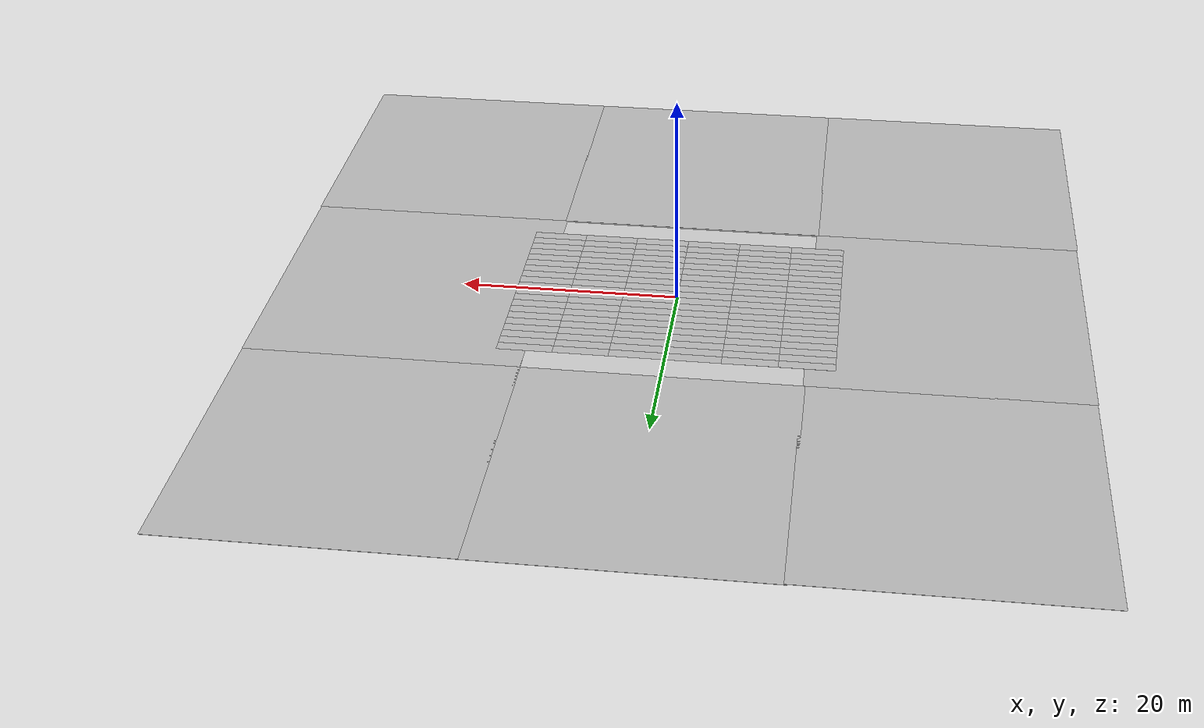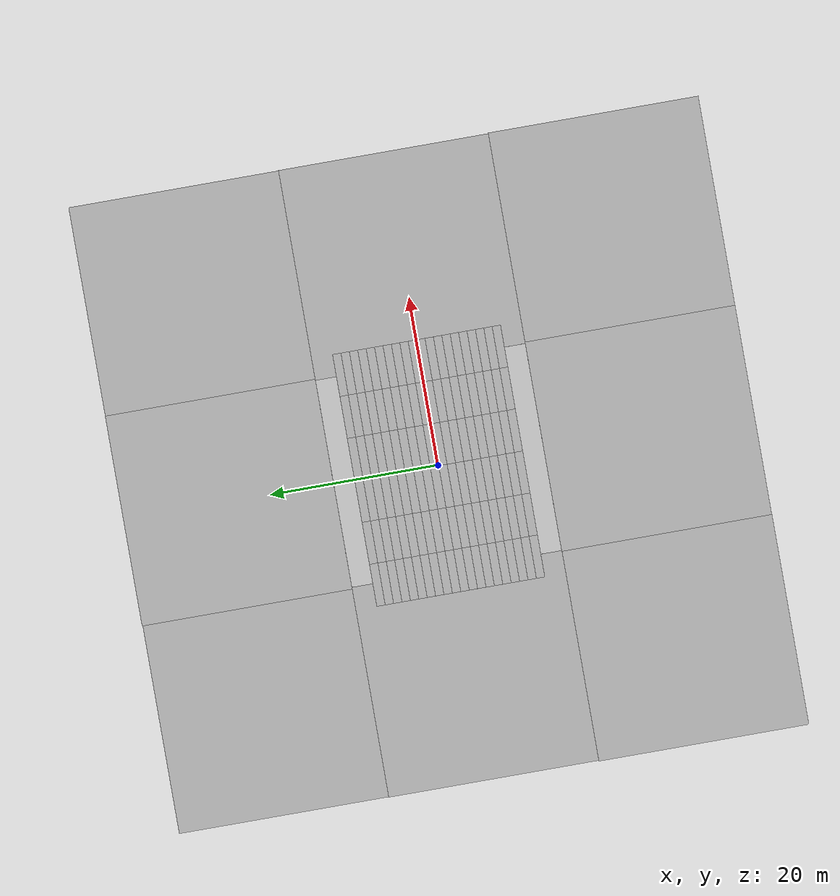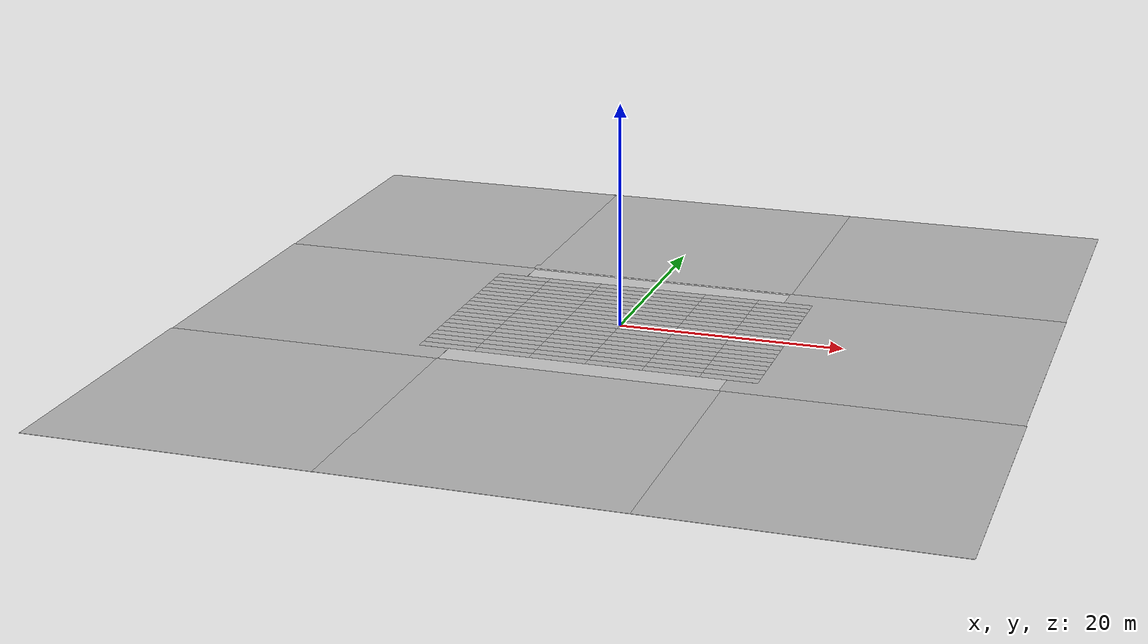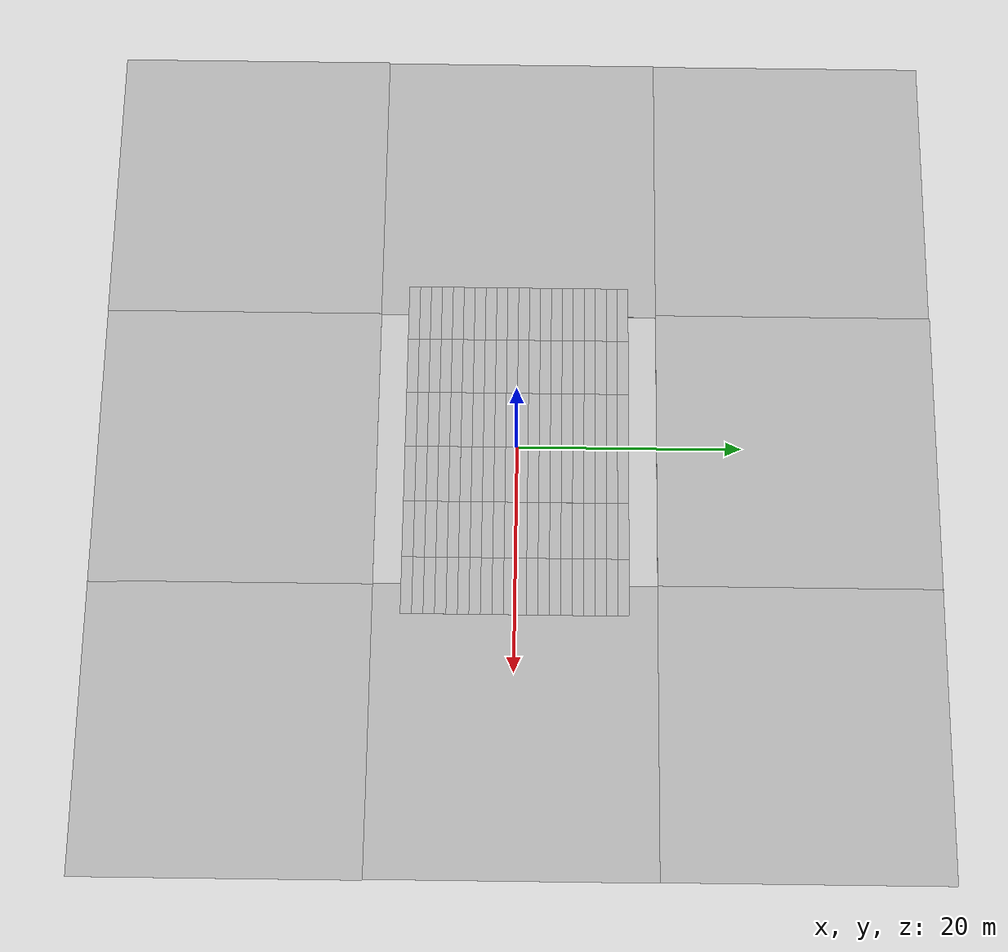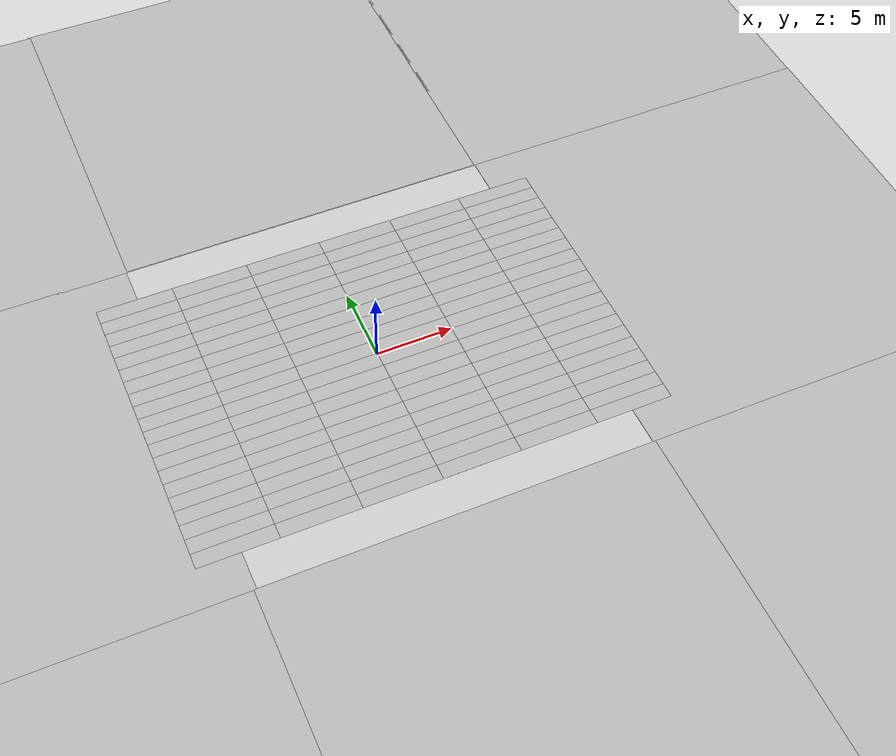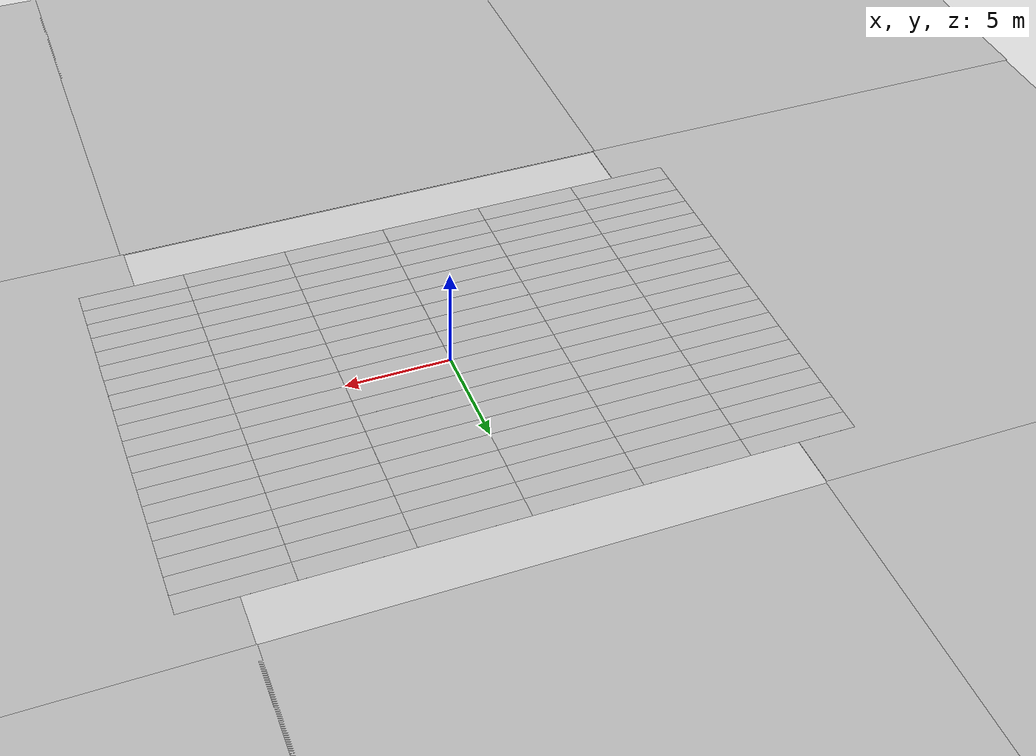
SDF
<sdf version="1.6">
 <world name="default">
  <light name="sun" type="directional">
   <pose>0 0 10 0 -0 0</pose>
   <diffuse>0.8 0.8 0.8 1</diffuse>
   <specular>0.2 0.2 0.2 1</specular>
   <attenuation>
    <range>1000</range>
    <constant>0.9</constant>
    <linear>0.01</linear>
    <quadratic>0.001</quadratic>
   </attenuation>
   <direction>-0.5 0.1 -0.9</direction>
  </light>
  <gravity>0 0 -9.8</gravity>
  <magnetic_field>6e-06 2.3e-05 -4.2e-05</magnetic_field>
  <atmosphere type="adiabatic"/>
  <physics name="default_physics" default="0" type="ode">
   <max_step_size>0.001</max_step_size>
   <real_time_factor>1</real_time_factor>
   <real_time_update_rate>1000</real_time_update_rate>
  </physics>
  <scene><ambient>0.4 0.4 0.4 1</ambient><background>0.7 0.7 0.7 1</background><shadows>1</shadows></scene>
  <spherical_coordinates>
   <surface_model>EARTH_WGS84</surface_model>
   <latitude_deg>0</latitude_deg>
   <longitude_deg>0</longitude_deg>
   <elevation>0</elevation>
   <heading_deg>0</heading_deg>
  </spherical_coordinates>
  <model name="cmp9767m_ground_3">
   <static>1</static>
   <link name="dirt">
    <collision name="collision">
     <geometry><plane><normal>0 0 1</normal><size>25 25</size></plane></geometry>
     <surface><friction><ode><mu>100</mu><mu2>50</mu2></ode></friction></surface>
    </collision>
    <visual name="visual">
     <cast_shadows>0</cast_shadows>
     <geometry><plane><normal>0 0 1</normal><size>25 25</size></plane></geometry>
     <material>
      <script>
       <uri>model://cmp9767m_ground_3/materials/scripts</uri>
       <uri>model://cmp9767m_ground_3/materials/textures</uri>
       <name>cmp9767m_ground_3/dirt</name>
      </script>
     </material>
    </visual>
   </link>
  </model>
  <model name="cmp9767m_ground_3_0">
   <static>1</static>
   <link name="dirt">
    <collision name="collision">
     <geometry><plane><normal>0 0 1</normal><size>25 25</size></plane></geometry>
     <surface><friction><ode><mu>100</mu><mu2>50</mu2></ode></friction></surface>
    </collision>
    <visual name="visual">
     <cast_shadows>0</cast_shadows>
     <geometry><plane><normal>0 0 1</normal><size>25 25</size></plane></geometry>
     <material>
      <script>
       <uri>model://cmp9767m_ground_3/materials/scripts</uri>
       <uri>model://cmp9767m_ground_3/materials/textures</uri>
       <name>cmp9767m_ground_3/dirt</name>
      </script>
     </material>
    </visual>
   </link>
   <pose>-0 25 0 0 -0 0</pose>
  </model>
  <model name="cmp9767m_ground_3_1">
   <static>1</static>
   <link name="dirt">
    <collision name="collision">
     <geometry><plane><normal>0 0 1</normal><size>25 25</size></plane></geometry>
     <surface><friction><ode><mu>100</mu><mu2>50</mu2></ode></friction></surface>
    </collision>
    <visual name="visual">
     <cast_shadows>0</cast_shadows>
     <geometry><plane><normal>0 0 1</normal><size>25 25</size></plane></geometry>
     <material>
      <script>
       <uri>model://cmp9767m_ground_3/materials/scripts</uri>
       <uri>model://cmp9767m_ground_3/materials/textures</uri>
       <name>cmp9767m_ground_3/dirt</name>
      </script>
     </material>
    </visual>
   </link>
   <pose>-24.7968 -0.006622 0 0 -0 0</pose>
  </model>
  <model name="cmp9767m_ground_3_2">
   <static>1</static>
   <link name="dirt">
    <collision name="collision">
     <geometry><plane><normal>0 0 1</normal><size>25 25</size></plane></geometry>
     <surface><friction><ode><mu>100</mu><mu2>50</mu2></ode></friction></surface>
    </collision>
    <visual name="visual">
     <cast_shadows>0</cast_shadows>
     <geometry><plane><normal>0 0 1</normal><size>25 25</size></plane></geometry>
     <material>
      <script>
       <uri>model://cmp9767m_ground_3/materials/scripts</uri>
       <uri>model://cmp9767m_ground_3/materials/textures</uri>
       <name>cmp9767m_ground_3/dirt</name>
      </script>
     </material>
    </visual>
   </link>
   <pose>-24.7414 24.922 0 0 -0 0</pose>
  </model>
  <model name="cmp9767m_ground_3_3">
   <static>1</static>
   <link name="dirt">
    <collision name="collision">
     <geometry><plane><normal>0 0 1</normal><size>25 25</size></plane></geometry>
     <surface><friction><ode><mu>100</mu><mu2>50</mu2></ode></friction></surface>
    </collision>
    <visual name="visual">
     <cast_shadows>0</cast_shadows>
     <geometry><plane><normal>0 0 1</normal><size>25 25</size></plane></geometry>
     <material>
      <script>
       <uri>model://cmp9767m_ground_3/materials/scripts</uri>
       <uri>model://cmp9767m_ground_3/materials/textures</uri>
       <name>cmp9767m_ground_3/dirt</name>
      </script>
     </material>
    </visual>
   </link>
   <pose>-24.8943 -25.0024 0 0 -0 0</pose>
  </model>
  <model name="cmp9767m_ground_3_4">
   <static>1</static>
   <link name="dirt">
    <collision name="collision">
     <geometry><plane><normal>0 0 1</normal><size>25 25</size></plane></geometry>
     <surface><friction><ode><mu>100</mu><mu2>50</mu2></ode></friction></surface>
    </collision>
    <visual name="visual">
     <cast_shadows>0</cast_shadows>
     <geometry><plane><normal>0 0 1</normal><size>25 25</size></plane></geometry>
     <material>
      <script>
       <uri>model://cmp9767m_ground_3/materials/scripts</uri>
       <uri>model://cmp9767m_ground_3/materials/textures</uri>
       <name>cmp9767m_ground_3/dirt</name>
      </script>
     </material>
    </visual>
   </link>
   <pose>0.027418 -24.9803 0 0 -0 0</pose>
  </model>
  <model name="cmp9767m_ground_3_5">
   <static>1</static>
   <link name="dirt">
    <collision name="collision">
     <geometry><plane><normal>0 0 1</normal><size>25 25</size></plane></geometry>
     <surface><friction><ode><mu>100</mu><mu2>50</mu2></ode></friction></surface>
    </collision>
    <visual name="visual">
     <cast_shadows>0</cast_shadows>
     <geometry><plane><normal>0 0 1</normal><size>25 25</size></plane></geometry>
     <material>
      <script>
       <uri>model://cmp9767m_ground_3/materials/scripts</uri>
       <uri>model://cmp9767m_ground_3/materials/textures</uri>
       <name>cmp9767m_ground_3/dirt</name>
      </script>
     </material>
    </visual>
   </link>
   <pose>24.9408 -24.9803 0 0 -0 0</pose>
  </model>
  <model name="cmp9767m_ground_3_6">
   <static>1</static>
   <link name="dirt">
    <collision name="collision">
     <geometry><plane><normal>0 0 1</normal><size>25 25</size></plane></geometry>
     <surface><friction><ode><mu>100</mu><mu2>50</mu2></ode></friction></surface>
    </collision>
    <visual name="visual">
     <cast_shadows>0</cast_shadows>
     <geometry><plane><normal>0 0 1</normal><size>25 25</size></plane></geometry>
     <material>
      <script>
       <uri>model://cmp9767m_ground_3/materials/scripts</uri>
       <uri>model://cmp9767m_ground_3/materials/textures</uri>
       <name>cmp9767m_ground_3/dirt</name>
      </script>
     </material>
    </visual>
   </link>
   <pose>24.8613 0.003309 0 0 -0 0</pose>
  </model>
  <model name="cmp9767m_ground_3_7">
   <static>1</static>
   <link name="dirt">
    <collision name="collision">
     <geometry><plane><normal>0 0 1</normal><size>25 25</size></plane></geometry>
     <surface><friction><ode><mu>100</mu><mu2>50</mu2></ode></friction></surface>
    </collision>
    <visual name="visual">
     <cast_shadows>0</cast_shadows>
     <geometry><plane><normal>0 0 1</normal><size>25 25</size></plane></geometry>
     <material>
      <script>
       <uri>model://cmp9767m_ground_3/materials/scripts</uri>
       <uri>model://cmp9767m_ground_3/materials/textures</uri>
       <name>cmp9767m_ground_3/dirt</name>
      </script>
     </material>
    </visual>
   </link>
   <pose>24.8226 24.9841 0 0 -0 0</pose>
  </model>
  <model name="crop_rows">
   <static>1</static>
   <link name="crop_rows">
    <pose>0 0 0.025 0 -0 0</pose>
    <collision name="collision">
     <geometry><plane><normal>0 0 1</normal><size>5 1</size></plane></geometry>
     <surface><friction><ode><mu>100</mu><mu2>50</mu2></ode></friction></surface>
    </collision>
    <visual name="visual">
     <cast_shadows>0</cast_shadows>
     <geometry><plane><normal>0 0 1</normal><size>5 1</size></plane></geometry>
     <material>
      <script>
       <uri>model://crop_rows/materials/scripts</uri>
       <uri>model://crop_rows/materials/textures</uri>
       <name>crop_rows/real_texture</name>
      </script>
     </material>
    </visual>
   </link>
   <pose>-2.5 -0.5 0 0 -0 0</pose>
  </model>
  <model name="crop_rows_0">
   <static>1</static>
   <link name="crop_rows">
    <pose>0 0 0.025 0 -0 0</pose>
    <collision name="collision">
     <geometry><plane><normal>0 0 1</normal><size>5 1</size></plane></geometry>
     <surface><friction><ode><mu>100</mu><mu2>50</mu2></ode></friction></surface>
    </collision>
    <visual name="visual">
     <cast_shadows>0</cast_shadows>
     <geometry><plane><normal>0 0 1</normal><size>5 1</size></plane></geometry>
     <material>
      <script>
       <uri>model://crop_rows/materials/scripts</uri>
       <uri>model://crop_rows/materials/textures</uri>
       <name>crop_rows/real_texture</name>
      </script>
     </material>
    </visual>
   </link>
   <pose>2.5 -0.5 0 0 -0 0</pose>
  </model>
  <model name="crop_rows_1">
   <static>1</static>
   <link name="crop_rows">
    <pose>0 0 0.025 0 -0 0</pose>
    <collision name="collision">
     <geometry><plane><normal>0 0 1</normal><size>5 1</size></plane></geometry>
     <surface><friction><ode><mu>100</mu><mu2>50</mu2></ode></friction></surface>
    </collision>
    <visual name="visual">
     <cast_shadows>0</cast_shadows>
     <geometry><plane><normal>0 0 1</normal><size>5 1</size></plane></geometry>
     <material>
      <script>
       <uri>model://crop_rows/materials/scripts</uri>
       <uri>model://crop_rows/materials/textures</uri>
       <name>crop_rows/real_texture</name>
      </script>
     </material>
    </visual>
   </link>
   <pose>-2.5 -1.5 0 0 -0 0</pose>
  </model>
  <model name="crop_rows_2">
   <static>1</static>
   <link name="crop_rows">
    <pose>0 0 0.025 0 -0 0</pose>
    <collision name="collision">
     <geometry><plane><normal>0 0 1</normal><size>5 1</size></plane></geometry>
     <surface><friction><ode><mu>100</mu><mu2>50</mu2></ode></friction></surface>
    </collision>
    <visual name="visual">
     <cast_shadows>0</cast_shadows>
     <geometry><plane><normal>0 0 1</normal><size>5 1</size></plane></geometry>
     <material>
      <script>
       <uri>model://crop_rows/materials/scripts</uri>
       <uri>model://crop_rows/materials/textures</uri>
       <name>crop_rows/real_texture</name>
      </script>
     </material>
    </visual>
   </link>
   <pose>2.5 -1.5 0 0 -0 0</pose>
  </model>
  <model name="crop_rows_3">
   <static>1</static>
   <link name="crop_rows">
    <pose>0 0 0.025 0 -0 0</pose>
    <collision name="collision">
     <geometry><plane><normal>0 0 1</normal><size>5 1</size></plane></geometry>
     <surface><friction><ode><mu>100</mu><mu2>50</mu2></ode></friction></surface>
    </collision>
    <visual name="visual">
     <cast_shadows>0</cast_shadows>
     <geometry><plane><normal>0 0 1</normal><size>5 1</size></plane></geometry>
     <material>
      <script>
       <uri>model://crop_rows/materials/scripts</uri>
       <uri>model://crop_rows/materials/textures</uri>
       <name>crop_rows/real_texture</name>
      </script>
     </material>
    </visual>
   </link>
   <pose>-2.5 -2.5 0 0 -0 0</pose>
  </model>
  <model name="crop_rows_4">
   <static>1</static>
   <link name="crop_rows">
    <pose>0 0 0.025 0 -0 0</pose>
    <collision name="collision">
     <geometry><plane><normal>0 0 1</normal><size>5 1</size></plane></geometry>
     <surface><friction><ode><mu>100</mu><mu2>50</mu2></ode></friction></surface>
    </collision>
    <visual name="visual">
     <cast_shadows>0</cast_shadows>
     <geometry><plane><normal>0 0 1</normal><size>5 1</size></plane></geometry>
     <material>
      <script>
       <uri>model://crop_rows/materials/scripts</uri>
       <uri>model://crop_rows/materials/textures</uri>
       <name>crop_rows/real_texture</name>
      </script>
     </material>
    </visual>
   </link>
   <pose>2.5 -2.5 0 0 -0 0</pose>
  </model>
  <model name="crop_rows_5">
   <static>1</static>
   <link name="crop_rows">
    <pose>0 0 0.025 0 -0 0</pose>
    <collision name="collision">
     <geometry><plane><normal>0 0 1</normal><size>5 1</size></plane></geometry>
     <surface><friction><ode><mu>100</mu><mu2>50</mu2></ode></friction></surface>
    </collision>
    <visual name="visual">
     <cast_shadows>0</cast_shadows>
     <geometry><plane><normal>0 0 1</normal><size>5 1</size></plane></geometry>
     <material>
      <script>
       <uri>model://crop_rows/materials/scripts</uri>
       <uri>model://crop_rows/materials/textures</uri>
       <name>crop_rows/real_texture</name>
      </script>
     </material>
    </visual>
   </link>
   <pose>-2.50602 -3.5 0 0 -0 0</pose>
  </model>
  <model name="crop_rows_6">
   <static>1</static>
   <link name="crop_rows">
    <pose>0 0 0.025 0 -0 0</pose>
    <collision name="collision">
     <geometry><plane><normal>0 0 1</normal><size>5 1</size></plane></geometry>
     <surface><friction><ode><mu>100</mu><mu2>50</mu2></ode></friction></surface>
    </collision>
    <visual name="visual">
     <cast_shadows>0</cast_shadows>
     <geometry><plane><normal>0 0 1</normal><size>5 1</size></plane></geometry>
     <material>
      <script>
       <uri>model://crop_rows/materials/scripts</uri>
       <uri>model://crop_rows/materials/textures</uri>
       <name>crop_rows/real_texture</name>
      </script>
     </material>
    </visual>
   </link>
   <pose>2.5 -3.5 0 0 -0 0</pose>
  </model>
  <model name="crop_rows_7">
   <static>1</static>
   <link name="crop_rows">
    <pose>0 0 0.025 0 -0 0</pose>
    <collision name="collision">
     <geometry><plane><normal>0 0 1</normal><size>5 1</size></plane></geometry>
     <surface><friction><ode><mu>100</mu><mu2>50</mu2></ode></friction></surface>
    </collision>
    <visual name="visual">
     <cast_shadows>0</cast_shadows>
     <geometry><plane><normal>0 0 1</normal><size>5 1</size></plane></geometry>
     <material>
      <script>
       <uri>model://crop_rows/materials/scripts</uri>
       <uri>model://crop_rows/materials/textures</uri>
       <name>crop_rows/real_texture</name>
      </script>
     </material>
    </visual>
   </link>
   <pose>2.5 -4.5 0 0 -0 0</pose>
  </model>
  <model name="crop_rows_8">
   <static>1</static>
   <link name="crop_rows">
    <pose>0 0 0.025 0 -0 0</pose>
    <collision name="collision">
     <geometry><plane><normal>0 0 1</normal><size>5 1</size></plane></geometry>
     <surface><friction><ode><mu>100</mu><mu2>50</mu2></ode></friction></surface>
    </collision>
    <visual name="visual">
     <cast_shadows>0</cast_shadows>
     <geometry><plane><normal>0 0 1</normal><size>5 1</size></plane></geometry>
     <material>
      <script>
       <uri>model://crop_rows/materials/scripts</uri>
       <uri>model://crop_rows/materials/textures</uri>
       <name>crop_rows/real_texture</name>
      </script>
     </material>
    </visual>
   </link>
   <pose>-2.5 -4.5 0 0 -0 0</pose>
  </model>
  <model name="crop_rows_9">
   <static>1</static>
   <link name="crop_rows">
    <pose>0 0 0.025 0 -0 0</pose>
    <collision name="collision">
     <geometry><plane><normal>0 0 1</normal><size>5 1</size></plane></geometry>
     <surface><friction><ode><mu>100</mu><mu2>50</mu2></ode></friction></surface>
    </collision>
    <visual name="visual">
     <cast_shadows>0</cast_shadows>
     <geometry><plane><normal>0 0 1</normal><size>5 1</size></plane></geometry>
     <material>
      <script>
       <uri>model://crop_rows/materials/scripts</uri>
       <uri>model://crop_rows/materials/textures</uri>
       <name>crop_rows/real_texture</name>
      </script>
     </material>
    </visual>
   </link>
   <pose>2.5 -5.5 0 0 -0 0</pose>
  </model>
  <model name="crop_rows_10">
   <static>1</static>
   <link name="crop_rows">
    <pose>0 0 0.025 0 -0 0</pose>
    <collision name="collision">
     <geometry><plane><normal>0 0 1</normal><size>5 1</size></plane></geometry>
     <surface><friction><ode><mu>100</mu><mu2>50</mu2></ode></friction></surface>
    </collision>
    <visual name="visual">
     <cast_shadows>0</cast_shadows>
     <geometry><plane><normal>0 0 1</normal><size>5 1</size></plane></geometry>
     <material>
      <script>
       <uri>model://crop_rows/materials/scripts</uri>
       <uri>model://crop_rows/materials/textures</uri>
       <name>crop_rows/real_texture</name>
      </script>
     </material>
    </visual>
   </link>
   <pose>-2.5 -5.5 0 0 -0 0</pose>
  </model>
  <model name="crop_rows_11">
   <static>1</static>
   <link name="crop_rows">
    <pose>0 0 0.025 0 -0 0</pose>
    <collision name="collision">
     <geometry><plane><normal>0 0 1</normal><size>5 1</size></plane></geometry>
     <surface><friction><ode><mu>100</mu><mu2>50</mu2></ode></friction></surface>
    </collision>
    <visual name="visual">
     <cast_shadows>0</cast_shadows>
     <geometry><plane><normal>0 0 1</normal><size>5 1</size></plane></geometry>
     <material>
      <script>
       <uri>model://crop_rows/materials/scripts</uri>
       <uri>model://crop_rows/materials/textures</uri>
       <name>crop_rows/real_texture</name>
      </script>
     </material>
    </visual>
   </link>
   <pose>2.5 0.5 0 0 -0 0</pose>
  </model>
  <model name="crop_rows_12">
   <static>1</static>
   <link name="crop_rows">
    <pose>0 0 0.025 0 -0 0</pose>
    <collision name="collision">
     <geometry><plane><normal>0 0 1</normal><size>5 1</size></plane></geometry>
     <surface><friction><ode><mu>100</mu><mu2>50</mu2></ode></friction></surface>
    </collision>
    <visual name="visual">
     <cast_shadows>0</cast_shadows>
     <geometry><plane><normal>0 0 1</normal><size>5 1</size></plane></geometry>
     <material>
      <script>
       <uri>model://crop_rows/materials/scripts</uri>
       <uri>model://crop_rows/materials/textures</uri>
       <name>crop_rows/real_texture</name>
      </script>
     </material>
    </visual>
   </link>
   <pose>2.5 1.5 0 0 -0 0</pose>
  </model>
  <model name="crop_rows_13">
   <static>1</static>
   <link name="crop_rows">
    <pose>0 0 0.025 0 -0 0</pose>
    <collision name="collision">
     <geometry><plane><normal>0 0 1</normal><size>5 1</size></plane></geometry>
     <surface><friction><ode><mu>100</mu><mu2>50</mu2></ode></friction></surface>
    </collision>
    <visual name="visual">
     <cast_shadows>0</cast_shadows>
     <geometry><plane><normal>0 0 1</normal><size>5 1</size></plane></geometry>
     <material>
      <script>
       <uri>model://crop_rows/materials/scripts</uri>
       <uri>model://crop_rows/materials/textures</uri>
       <name>crop_rows/real_texture</name>
      </script>
     </material>
    </visual>
   </link>
   <pose>2.50339 2.50065 0 0 -0 0</pose>
  </model>
  <model name="crop_rows_14">
   <static>1</static>
   <link name="crop_rows">
    <pose>0 0 0.025 0 -0 0</pose>
    <collision name="collision">
     <geometry><plane><normal>0 0 1</normal><size>5 1</size></plane></geometry>
     <surface><friction><ode><mu>100</mu><mu2>50</mu2></ode></friction></surface>
    </collision>
    <visual name="visual">
     <cast_shadows>0</cast_shadows>
     <geometry><plane><normal>0 0 1</normal><size>5 1</size></plane></geometry>
     <material>
      <script>
       <uri>model://crop_rows/materials/scripts</uri>
       <uri>model://crop_rows/materials/textures</uri>
       <name>crop_rows/real_texture</name>
      </script>
     </material>
    </visual>
   </link>
   <pose>2.5 3.5 0 0 -0 0</pose>
  </model>
  <model name="crop_rows_15">
   <static>1</static>
   <link name="crop_rows">
    <pose>0 0 0.025 0 -0 0</pose>
    <collision name="collision">
     <geometry><plane><normal>0 0 1</normal><size>5 1</size></plane></geometry>
     <surface><friction><ode><mu>100</mu><mu2>50</mu2></ode></friction></surface>
    </collision>
    <visual name="visual">
     <cast_shadows>0</cast_shadows>
     <geometry><plane><normal>0 0 1</normal><size>5 1</size></plane></geometry>
     <material>
      <script>
       <uri>model://crop_rows/materials/scripts</uri>
       <uri>model://crop_rows/materials/textures</uri>
       <name>crop_rows/real_texture</name>
      </script>
     </material>
    </visual>
   </link>
   <pose>-2.5 0.5 0 0 -0 0</pose>
  </model>
  <model name="crop_rows_16">
   <static>1</static>
   <link name="crop_rows">
    <pose>0 0 0.025 0 -0 0</pose>
    <collision name="collision">
     <geometry><plane><normal>0 0 1</normal><size>5 1</size></plane></geometry>
     <surface><friction><ode><mu>100</mu><mu2>50</mu2></ode></friction></surface>
    </collision>
    <visual name="visual">
     <cast_shadows>0</cast_shadows>
     <geometry><plane><normal>0 0 1</normal><size>5 1</size></plane></geometry>
     <material>
      <script>
       <uri>model://crop_rows/materials/scripts</uri>
       <uri>model://crop_rows/materials/textures</uri>
       <name>crop_rows/real_texture</name>
      </script>
     </material>
    </visual>
   </link>
   <pose>-2.5 1.5 0 0 -0 0</pose>
  </model>
  <model name="crop_rows_17">
   <static>1</static>
   <link name="crop_rows">
    <pose>0 0 0.025 0 -0 0</pose>
    <collision name="collision">
     <geometry><plane><normal>0 0 1</normal><size>5 1</size></plane></geometry>
     <surface><friction><ode><mu>100</mu><mu2>50</mu2></ode></friction></surface>
    </collision>
    <visual name="visual">
     <cast_shadows>0</cast_shadows>
     <geometry><plane><normal>0 0 1</normal><size>5 1</size></plane></geometry>
     <material>
      <script>
       <uri>model://crop_rows/materials/scripts</uri>
       <uri>model://crop_rows/materials/textures</uri>
       <name>crop_rows/real_texture</name>
      </script>
     </material>
    </visual>
   </link>
   <pose>-2.5 2.5 0 0 -0 0</pose>
  </model>
  <model name="crop_rows_18">
   <static>1</static>
   <link name="crop_rows">
    <pose>0 0 0.025 0 -0 0</pose>
    <collision name="collision">
     <geometry><plane><normal>0 0 1</normal><size>5 1</size></plane></geometry>
     <surface><friction><ode><mu>100</mu><mu2>50</mu2></ode></friction></surface>
    </collision>
    <visual name="visual">
     <cast_shadows>0</cast_shadows>
     <geometry><plane><normal>0 0 1</normal><size>5 1</size></plane></geometry>
     <material>
      <script>
       <uri>model://crop_rows/materials/scripts</uri>
       <uri>model://crop_rows/materials/textures</uri>
       <name>crop_rows/real_texture</name>
      </script>
     </material>
    </visual>
   </link>
   <pose>-2.5 3.5 0 0 -0 0</pose>
  </model>
  <model name="crop_rows_19">
   <static>1</static>
   <link name="crop_rows">
    <pose>0 0 0.025 0 -0 0</pose>
    <collision name="collision">
     <geometry><plane><normal>0 0 1</normal><size>5 1</size></plane></geometry>
     <surface><friction><ode><mu>100</mu><mu2>50</mu2></ode></friction></surface>
    </collision>
    <visual name="visual">
     <cast_shadows>0</cast_shadows>
     <geometry><plane><normal>0 0 1</normal><size>5 1</size></plane></geometry>
     <material>
      <script>
       <uri>model://crop_rows/materials/scripts</uri>
       <uri>model://crop_rows/materials/textures</uri>
       <name>crop_rows/real_texture</name>
      </script>
     </material>
    </visual>
   </link>
   <pose>7.5 -5.5 0 0 -0 0</pose>
  </model>
  <model name="crop_rows_20">
   <static>1</static>
   <link name="crop_rows">
    <pose>0 0 0.025 0 -0 0</pose>
    <collision name="collision">
     <geometry><plane><normal>0 0 1</normal><size>5 1</size></plane></geometry>
     <surface><friction><ode><mu>100</mu><mu2>50</mu2></ode></friction></surface>
    </collision>
    <visual name="visual">
     <cast_shadows>0</cast_shadows>
     <geometry><plane><normal>0 0 1</normal><size>5 1</size></plane></geometry>
     <material>
      <script>
       <uri>model://crop_rows/materials/scripts</uri>
       <uri>model://crop_rows/materials/textures</uri>
       <name>crop_rows/real_texture</name>
      </script>
     </material>
    </visual>
   </link>
   <pose>7.5 -4.5 0 0 -0 0</pose>
  </model>
  <model name="crop_rows_21">
   <static>1</static>
   <link name="crop_rows">
    <pose>0 0 0.025 0 -0 0</pose>
    <collision name="collision">
     <geometry><plane><normal>0 0 1</normal><size>5 1</size></plane></geometry>
     <surface><friction><ode><mu>100</mu><mu2>50</mu2></ode></friction></surface>
    </collision>
    <visual name="visual">
     <cast_shadows>0</cast_shadows>
     <geometry><plane><normal>0 0 1</normal><size>5 1</size></plane></geometry>
     <material>
      <script>
       <uri>model://crop_rows/materials/scripts</uri>
       <uri>model://crop_rows/materials/textures</uri>
       <name>crop_rows/real_texture</name>
      </script>
     </material>
    </visual>
   </link>
   <pose>7.5 -3.5 0 0 -0 0</pose>
  </model>
  <model name="crop_rows_22">
   <static>1</static>
   <link name="crop_rows">
    <pose>0 0 0.025 0 -0 0</pose>
    <collision name="collision">
     <geometry><plane><normal>0 0 1</normal><size>5 1</size></plane></geometry>
     <surface><friction><ode><mu>100</mu><mu2>50</mu2></ode></friction></surface>
    </collision>
    <visual name="visual">
     <cast_shadows>0</cast_shadows>
     <geometry><plane><normal>0 0 1</normal><size>5 1</size></plane></geometry>
     <material>
      <script>
       <uri>model://crop_rows/materials/scripts</uri>
       <uri>model://crop_rows/materials/textures</uri>
       <name>crop_rows/real_texture</name>
      </script>
     </material>
    </visual>
   </link>
   <pose>7.5 -2.5 0 0 -0 0</pose>
  </model>
  <model name="crop_rows_23">
   <static>1</static>
   <link name="crop_rows">
    <pose>0 0 0.025 0 -0 0</pose>
    <collision name="collision">
     <geometry><plane><normal>0 0 1</normal><size>5 1</size></plane></geometry>
     <surface><friction><ode><mu>100</mu><mu2>50</mu2></ode></friction></surface>
    </collision>
    <visual name="visual">
     <cast_shadows>0</cast_shadows>
     <geometry><plane><normal>0 0 1</normal><size>5 1</size></plane></geometry>
     <material>
      <script>
       <uri>model://crop_rows/materials/scripts</uri>
       <uri>model://crop_rows/materials/textures</uri>
       <name>crop_rows/real_texture</name>
      </script>
     </material>
    </visual>
   </link>
   <pose>7.5 -1.5 0 0 -0 0</pose>
  </model>
  <model name="crop_rows_24">
   <static>1</static>
   <link name="crop_rows">
    <pose>0 0 0.025 0 -0 0</pose>
    <collision name="collision">
     <geometry><plane><normal>0 0 1</normal><size>5 1</size></plane></geometry>
     <surface><friction><ode><mu>100</mu><mu2>50</mu2></ode></friction></surface>
    </collision>
    <visual name="visual">
     <cast_shadows>0</cast_shadows>
     <geometry><plane><normal>0 0 1</normal><size>5 1</size></plane></geometry>
     <material>
      <script>
       <uri>model://crop_rows/materials/scripts</uri>
       <uri>model://crop_rows/materials/textures</uri>
       <name>crop_rows/real_texture</name>
      </script>
     </material>
    </visual>
   </link>
   <pose>7.5 -0.5 0 0 -0 0</pose>
  </model>
  <model name="crop_rows_25">
   <static>1</static>
   <link name="crop_rows">
    <pose>0 0 0.025 0 -0 0</pose>
    <collision name="collision">
     <geometry><plane><normal>0 0 1</normal><size>5 1</size></plane></geometry>
     <surface><friction><ode><mu>100</mu><mu2>50</mu2></ode></friction></surface>
    </collision>
    <visual name="visual">
     <cast_shadows>0</cast_shadows>
     <geometry><plane><normal>0 0 1</normal><size>5 1</size></plane></geometry>
     <material>
      <script>
       <uri>model://crop_rows/materials/scripts</uri>
       <uri>model://crop_rows/materials/textures</uri>
       <name>crop_rows/real_texture</name>
      </script>
     </material>
    </visual>
   </link>
   <pose>7.5 0.5 0 0 -0 0</pose>
  </model>
  <model name="crop_rows_26">
   <static>1</static>
   <link name="crop_rows">
    <pose>0 0 0.025 0 -0 0</pose>
    <collision name="collision">
     <geometry><plane><normal>0 0 1</normal><size>5 1</size></plane></geometry>
     <surface><friction><ode><mu>100</mu><mu2>50</mu2></ode></friction></surface>
    </collision>
    <visual name="visual">
     <cast_shadows>0</cast_shadows>
     <geometry><plane><normal>0 0 1</normal><size>5 1</size></plane></geometry>
     <material>
      <script>
       <uri>model://crop_rows/materials/scripts</uri>
       <uri>model://crop_rows/materials/textures</uri>
       <name>crop_rows/real_texture</name>
      </script>
     </material>
    </visual>
   </link>
   <pose>7.5 1.5 0 0 -0 0</pose>
  </model>
  <model name="crop_rows_27">
   <static>1</static>
   <link name="crop_rows">
    <pose>0 0 0.025 0 -0 0</pose>
    <collision name="collision">
     <geometry><plane><normal>0 0 1</normal><size>5 1</size></plane></geometry>
     <surface><friction><ode><mu>100</mu><mu2>50</mu2></ode></friction></surface>
    </collision>
    <visual name="visual">
     <cast_shadows>0</cast_shadows>
     <geometry><plane><normal>0 0 1</normal><size>5 1</size></plane></geometry>
     <material>
      <script>
       <uri>model://crop_rows/materials/scripts</uri>
       <uri>model://crop_rows/materials/textures</uri>
       <name>crop_rows/real_texture</name>
      </script>
     </material>
    </visual>
   </link>
   <pose>7.5 2.5 0 0 -0 0</pose>
  </model>
  <model name="crop_rows_28">
   <static>1</static>
   <link name="crop_rows">
    <pose>0 0 0.025 0 -0 0</pose>
    <collision name="collision">
     <geometry><plane><normal>0 0 1</normal><size>5 1</size></plane></geometry>
     <surface><friction><ode><mu>100</mu><mu2>50</mu2></ode></friction></surface>
    </collision>
    <visual name="visual">
     <cast_shadows>0</cast_shadows>
     <geometry><plane><normal>0 0 1</normal><size>5 1</size></plane></geometry>
     <material>
      <script>
       <uri>model://crop_rows/materials/scripts</uri>
       <uri>model://crop_rows/materials/textures</uri>
       <name>crop_rows/real_texture</name>
      </script>
     </material>
    </visual>
   </link>
   <pose>7.5 3.5 0 0 -0 0</pose>
  </model>
  <model name="crop_rows_29">
   <static>1</static>
   <link name="crop_rows">
    <pose>0 0 0.025 0 -0 0</pose>
    <collision name="collision">
     <geometry><plane><normal>0 0 1</normal><size>5 1</size></plane></geometry>
     <surface><friction><ode><mu>100</mu><mu2>50</mu2></ode></friction></surface>
    </collision>
    <visual name="visual">
     <cast_shadows>0</cast_shadows>
     <geometry><plane><normal>0 0 1</normal><size>5 1</size></plane></geometry>
     <material>
      <script>
       <uri>model://crop_rows/materials/scripts</uri>
       <uri>model://crop_rows/materials/textures</uri>
       <name>crop_rows/real_texture</name>
      </script>
     </material>
    </visual>
   </link>
   <pose>-2.5 4.5 0 0 -0 0</pose>
  </model>
  <model name="crop_rows_30">
   <static>1</static>
   <link name="crop_rows">
    <pose>0 0 0.025 0 -0 0</pose>
    <collision name="collision">
     <geometry><plane><normal>0 0 1</normal><size>5 1</size></plane></geometry>
     <surface><friction><ode><mu>100</mu><mu2>50</mu2></ode></friction></surface>
    </collision>
    <visual name="visual">
     <cast_shadows>0</cast_shadows>
     <geometry><plane><normal>0 0 1</normal><size>5 1</size></plane></geometry>
     <material>
      <script>
       <uri>model://crop_rows/materials/scripts</uri>
       <uri>model://crop_rows/materials/textures</uri>
       <name>crop_rows/real_texture</name>
      </script>
     </material>
    </visual>
   </link>
   <pose>2.5 4.5 0 0 -0 0</pose>
  </model>
  <model name="crop_rows_31">
   <static>1</static>
   <link name="crop_rows">
    <pose>0 0 0.025 0 -0 0</pose>
    <collision name="collision">
     <geometry><plane><normal>0 0 1</normal><size>5 1</size></plane></geometry>
     <surface><friction><ode><mu>100</mu><mu2>50</mu2></ode></friction></surface>
    </collision>
    <visual name="visual">
     <cast_shadows>0</cast_shadows>
     <geometry><plane><normal>0 0 1</normal><size>5 1</size></plane></geometry>
     <material>
      <script>
       <uri>model://crop_rows/materials/scripts</uri>
       <uri>model://crop_rows/materials/textures</uri>
       <name>crop_rows/real_texture</name>
      </script>
     </material>
    </visual>
   </link>
   <pose>7.50726 4.5 0 0 -0 0</pose>
  </model>
  <model name="crop_rows_32">
   <static>1</static>
   <link name="crop_rows">
    <pose>0 0 0.025 0 -0 0</pose>
    <collision name="collision">
     <geometry><plane><normal>0 0 1</normal><size>5 1</size></plane></geometry>
     <surface><friction><ode><mu>100</mu><mu2>50</mu2></ode></friction></surface>
    </collision>
    <visual name="visual">
     <cast_shadows>0</cast_shadows>
     <geometry><plane><normal>0 0 1</normal><size>5 1</size></plane></geometry>
     <material>
      <script>
       <uri>model://crop_rows/materials/scripts</uri>
       <uri>model://crop_rows/materials/textures</uri>
       <name>crop_rows/real_texture</name>
      </script>
     </material>
    </visual>
   </link>
   <pose>-2.5 5.5 0 0 -0 0</pose>
  </model>
  <model name="crop_rows_33">
   <static>1</static>
   <link name="crop_rows">
    <pose>0 0 0.025 0 -0 0</pose>
    <collision name="collision">
     <geometry><plane><normal>0 0 1</normal><size>5 1</size></plane></geometry>
     <surface><friction><ode><mu>100</mu><mu2>50</mu2></ode></friction></surface>
    </collision>
    <visual name="visual">
     <cast_shadows>0</cast_shadows>
     <geometry><plane><normal>0 0 1</normal><size>5 1</size></plane></geometry>
     <material>
      <script>
       <uri>model://crop_rows/materials/scripts</uri>
       <uri>model://crop_rows/materials/textures</uri>
       <name>crop_rows/real_texture</name>
      </script>
     </material>
    </visual>
   </link>
   <pose>2.5 5.5 0 0 -0 0</pose>
  </model>
  <model name="crop_rows_34">
   <static>1</static>
   <link name="crop_rows">
    <pose>0 0 0.025 0 -0 0</pose>
    <collision name="collision">
     <geometry><plane><normal>0 0 1</normal><size>5 1</size></plane></geometry>
     <surface><friction><ode><mu>100</mu><mu2>50</mu2></ode></friction></surface>
    </collision>
    <visual name="visual">
     <cast_shadows>0</cast_shadows>
     <geometry><plane><normal>0 0 1</normal><size>5 1</size></plane></geometry>
     <material>
      <script>
       <uri>model://crop_rows/materials/scripts</uri>
       <uri>model://crop_rows/materials/textures</uri>
       <name>crop_rows/real_texture</name>
      </script>
     </material>
    </visual>
   </link>
   <pose>7.5 5.5 0 0 -0 0</pose>
  </model>
  <model name="crop_rows_35">
   <static>1</static>
   <link name="crop_rows">
    <pose>0 0 0.025 0 -0 0</pose>
    <collision name="collision">
     <geometry><plane><normal>0 0 1</normal><size>5 1</size></plane></geometry>
     <surface><friction><ode><mu>100</mu><mu2>50</mu2></ode></friction></surface>
    </collision>
    <visual name="visual">
     <cast_shadows>0</cast_shadows>
     <geometry><plane><normal>0 0 1</normal><size>5 1</size></plane></geometry>
     <material>
      <script>
       <uri>model://crop_rows/materials/scripts</uri>
       <uri>model://crop_rows/materials/textures</uri>
       <name>crop_rows/real_texture</name>
      </script>
     </material>
    </visual>
   </link>
   <pose>-2.5 6.5 0 0 -0 0</pose>
  </model>
  <model name="crop_rows_36">
   <static>1</static>
   <link name="crop_rows">
    <pose>0 0 0.025 0 -0 0</pose>
    <collision name="collision">
     <geometry><plane><normal>0 0 1</normal><size>5 1</size></plane></geometry>
     <surface><friction><ode><mu>100</mu><mu2>50</mu2></ode></friction></surface>
    </collision>
    <visual name="visual">
     <cast_shadows>0</cast_shadows>
     <geometry><plane><normal>0 0 1</normal><size>5 1</size></plane></geometry>
     <material>
      <script>
       <uri>model://crop_rows/materials/scripts</uri>
       <uri>model://crop_rows/materials/textures</uri>
       <name>crop_rows/real_texture</name>
      </script>
     </material>
    </visual>
   </link>
   <pose>2.5 6.5 0 0 -0 0</pose>
  </model>
  <model name="crop_rows_37">
   <static>1</static>
   <link name="crop_rows">
    <pose>0 0 0.025 0 -0 0</pose>
    <collision name="collision">
     <geometry><plane><normal>0 0 1</normal><size>5 1</size></plane></geometry>
     <surface><friction><ode><mu>100</mu><mu2>50</mu2></ode></friction></surface>
    </collision>
    <visual name="visual">
     <cast_shadows>0</cast_shadows>
     <geometry><plane><normal>0 0 1</normal><size>5 1</size></plane></geometry>
     <material>
      <script>
       <uri>model://crop_rows/materials/scripts</uri>
       <uri>model://crop_rows/materials/textures</uri>
       <name>crop_rows/real_texture</name>
      </script>
     </material>
    </visual>
   </link>
   <pose>7.5 6.5 0 0 -0 0</pose>
  </model>
  <model name="crop_rows_38">
   <static>1</static>
   <link name="crop_rows">
    <pose>0 0 0.025 0 -0 0</pose>
    <collision name="collision">
     <geometry><plane><normal>0 0 1</normal><size>5 1</size></plane></geometry>
     <surface><friction><ode><mu>100</mu><mu2>50</mu2></ode></friction></surface>
    </collision>
    <visual name="visual">
     <cast_shadows>0</cast_shadows>
     <geometry><plane><normal>0 0 1</normal><size>5 1</size></plane></geometry>
     <material>
      <script>
       <uri>model://crop_rows/materials/scripts</uri>
       <uri>model://crop_rows/materials/textures</uri>
       <name>crop_rows/real_texture</name>
      </script>
     </material>
    </visual>
   </link>
   <pose>-2.5 -6.5 0 0 -0 0</pose>
  </model>
  <model name="crop_rows_39">
   <static>1</static>
   <link name="crop_rows">
    <pose>0 0 0.025 0 -0 0</pose>
    <collision name="collision">
     <geometry><plane><normal>0 0 1</normal><size>5 1</size></plane></geometry>
     <surface><friction><ode><mu>100</mu><mu2>50</mu2></ode></friction></surface>
    </collision>
    <visual name="visual">
     <cast_shadows>0</cast_shadows>
     <geometry><plane><normal>0 0 1</normal><size>5 1</size></plane></geometry>
     <material>
      <script>
       <uri>model://crop_rows/materials/scripts</uri>
       <uri>model://crop_rows/materials/textures</uri>
       <name>crop_rows/real_texture</name>
      </script>
     </material>
    </visual>
   </link>
   <pose>2.5 -6.5 0 0 -0 0</pose>
  </model>
  <model name="crop_rows_40">
   <static>1</static>
   <link name="crop_rows">
    <pose>0 0 0.025 0 -0 0</pose>
    <collision name="collision">
     <geometry><plane><normal>0 0 1</normal><size>5 1</size></plane></geometry>
     <surface><friction><ode><mu>100</mu><mu2>50</mu2></ode></friction></surface>
    </collision>
    <visual name="visual">
     <cast_shadows>0</cast_shadows>
     <geometry><plane><normal>0 0 1</normal><size>5 1</size></plane></geometry>
     <material>
      <script>
       <uri>model://crop_rows/materials/scripts</uri>
       <uri>model://crop_rows/materials/textures</uri>
       <name>crop_rows/real_texture</name>
      </script>
     </material>
    </visual>
   </link>
   <pose>7.5 -6.5 0 0 -0 0</pose>
  </model>
  <model name="crop_rows_41">
   <static>1</static>
   <link name="crop_rows">
    <pose>0 0 0.025 0 -0 0</pose>
    <collision name="collision">
     <geometry><plane><normal>0 0 1</normal><size>5 1</size></plane></geometry>
     <surface><friction><ode><mu>100</mu><mu2>50</mu2></ode></friction></surface>
    </collision>
    <visual name="visual">
     <cast_shadows>0</cast_shadows>
     <geometry><plane><normal>0 0 1</normal><size>5 1</size></plane></geometry>
     <material>
      <script>
       <uri>model://crop_rows/materials/scripts</uri>
       <uri>model://crop_rows/materials/textures</uri>
       <name>crop_rows/real_texture</name>
      </script>
     </material>
    </visual>
   </link>
   <pose>-2.5 7.5 0 0 -0 0</pose>
  </model>
  <model name="crop_rows_42">
   <static>1</static>
   <link name="crop_rows">
    <pose>0 0 0.025 0 -0 0</pose>
    <collision name="collision">
     <geometry><plane><normal>0 0 1</normal><size>5 1</size></plane></geometry>
     <surface><friction><ode><mu>100</mu><mu2>50</mu2></ode></friction></surface>
    </collision>
    <visual name="visual">
     <cast_shadows>0</cast_shadows>
     <geometry><plane><normal>0 0 1</normal><size>5 1</size></plane></geometry>
     <material>
      <script>
       <uri>model://crop_rows/materials/scripts</uri>
       <uri>model://crop_rows/materials/textures</uri>
       <name>crop_rows/real_texture</name>
      </script>
     </material>
    </visual>
   </link>
   <pose>2.5 7.5 0 0 -0 0</pose>
  </model>
  <model name="crop_rows_43">
   <static>1</static>
   <link name="crop_rows">
    <pose>0 0 0.025 0 -0 0</pose>
    <collision name="collision">
     <geometry><plane><normal>0 0 1</normal><size>5 1</size></plane></geometry>
     <surface><friction><ode><mu>100</mu><mu2>50</mu2></ode></friction></surface>
    </collision>
    <visual name="visual">
     <cast_shadows>0</cast_shadows>
     <geometry><plane><normal>0 0 1</normal><size>5 1</size></plane></geometry>
     <material>
      <script>
       <uri>model://crop_rows/materials/scripts</uri>
       <uri>model://crop_rows/materials/textures</uri>
       <name>crop_rows/real_texture</name>
      </script>
     </material>
    </visual>
   </link>
   <pose>7.5 7.5 0 0 -0 0</pose>
  </model>
  <model name="crop_rows_44">
   <static>1</static>
   <link name="crop_rows">
    <pose>0 0 0.025 0 -0 0</pose>
    <collision name="collision">
     <geometry><plane><normal>0 0 1</normal><size>5 1</size></plane></geometry>
     <surface><friction><ode><mu>100</mu><mu2>50</mu2></ode></friction></surface>
    </collision>
    <visual name="visual">
     <cast_shadows>0</cast_shadows>
     <geometry><plane><normal>0 0 1</normal><size>5 1</size></plane></geometry>
     <material>
      <script>
       <uri>model://crop_rows/materials/scripts</uri>
       <uri>model://crop_rows/materials/textures</uri>
       <name>crop_rows/real_texture</name>
      </script>
     </material>
    </visual>
   </link>
   <pose>-2.5 -7.5 0 0 -0 0</pose>
  </model>
  <model name="crop_rows_45">
   <static>1</static>
   <link name="crop_rows">
    <pose>0 0 0.025 0 -0 0</pose>
    <collision name="collision">
     <geometry><plane><normal>0 0 1</normal><size>5 1</size></plane></geometry>
     <surface><friction><ode><mu>100</mu><mu2>50</mu2></ode></friction></surface>
    </collision>
    <visual name="visual">
     <cast_shadows>0</cast_shadows>
     <geometry><plane><normal>0 0 1</normal><size>5 1</size></plane></geometry>
     <material>
      <script>
       <uri>model://crop_rows/materials/scripts</uri>
       <uri>model://crop_rows/materials/textures</uri>
       <name>crop_rows/real_texture</name>
      </script>
     </material>
    </visual>
   </link>
   <pose>2.5 -7.5 0 0 -0 0</pose>
  </model>
  <model name="crop_rows_46">
   <static>1</static>
   <link name="crop_rows">
    <pose>0 0 0.025 0 -0 0</pose>
    <collision name="collision">
     <geometry><plane><normal>0 0 1</normal><size>5 1</size></plane></geometry>
     <surface><friction><ode><mu>100</mu><mu2>50</mu2></ode></friction></surface>
    </collision>
    <visual name="visual">
     <cast_shadows>0</cast_shadows>
     <geometry><plane><normal>0 0 1</normal><size>5 1</size></plane></geometry>
     <material>
      <script>
       <uri>model://crop_rows/materials/scripts</uri>
       <uri>model://crop_rows/materials/textures</uri>
       <name>crop_rows/real_texture</name>
      </script>
     </material>
    </visual>
   </link>
   <pose>7.5 -7.5 0 0 -0 0</pose>
  </model>
  <model name="crop_rows_47">
   <static>1</static>
   <link name="crop_rows">
    <pose>0 0 0.025 0 -0 0</pose>
    <collision name="collision">
     <geometry><plane><normal>0 0 1</normal><size>5 1</size></plane></geometry>
     <surface><friction><ode><mu>100</mu><mu2>50</mu2></ode></friction></surface>
    </collision>
    <visual name="visual">
     <cast_shadows>0</cast_shadows>
     <geometry><plane><normal>0 0 1</normal><size>5 1</size></plane></geometry>
     <material>
      <script>
       <uri>model://crop_rows/materials/scripts</uri>
       <uri>model://crop_rows/materials/textures</uri>
       <name>crop_rows/real_texture</name>
      </script>
     </material>
    </visual>
   </link>
   <pose>12.5 -7.5 0 0 -0 0</pose>
  </model>
  <model name="crop_rows_48">
   <static>1</static>
   <link name="crop_rows">
    <pose>0 0 0.025 0 -0 0</pose>
    <collision name="collision">
     <geometry><plane><normal>0 0 1</normal><size>5 1</size></plane></geometry>
     <surface><friction><ode><mu>100</mu><mu2>50</mu2></ode></friction></surface>
    </collision>
    <visual name="visual">
     <cast_shadows>0</cast_shadows>
     <geometry><plane><normal>0 0 1</normal><size>5 1</size></plane></geometry>
     <material>
      <script>
       <uri>model://crop_rows/materials/scripts</uri>
       <uri>model://crop_rows/materials/textures</uri>
       <name>crop_rows/real_texture</name>
      </script>
     </material>
    </visual>
   </link>
   <pose>12.5 -6.5 0 0 -0 0</pose>
  </model>
  <model name="crop_rows_49">
   <static>1</static>
   <link name="crop_rows">
    <pose>0 0 0.025 0 -0 0</pose>
    <collision name="collision">
     <geometry><plane><normal>0 0 1</normal><size>5 1</size></plane></geometry>
     <surface><friction><ode><mu>100</mu><mu2>50</mu2></ode></friction></surface>
    </collision>
    <visual name="visual">
     <cast_shadows>0</cast_shadows>
     <geometry><plane><normal>0 0 1</normal><size>5 1</size></plane></geometry>
     <material>
      <script>
       <uri>model://crop_rows/materials/scripts</uri>
       <uri>model://crop_rows/materials/textures</uri>
       <name>crop_rows/real_texture</name>
      </script>
     </material>
    </visual>
   </link>
   <pose>12.5 -5.5 0 0 -0 0</pose>
  </model>
  <model name="crop_rows_50">
   <static>1</static>
   <link name="crop_rows">
    <pose>0 0 0.025 0 -0 0</pose>
    <collision name="collision">
     <geometry><plane><normal>0 0 1</normal><size>5 1</size></plane></geometry>
     <surface><friction><ode><mu>100</mu><mu2>50</mu2></ode></friction></surface>
    </collision>
    <visual name="visual">
     <cast_shadows>0</cast_shadows>
     <geometry><plane><normal>0 0 1</normal><size>5 1</size></plane></geometry>
     <material>
      <script>
       <uri>model://crop_rows/materials/scripts</uri>
       <uri>model://crop_rows/materials/textures</uri>
       <name>crop_rows/real_texture</name>
      </script>
     </material>
    </visual>
   </link>
   <pose>12.509 -4.5 0 0 -0 0</pose>
  </model>
  <model name="crop_rows_51">
   <static>1</static>
   <link name="crop_rows">
    <pose>0 0 0.025 0 -0 0</pose>
    <collision name="collision">
     <geometry><plane><normal>0 0 1</normal><size>5 1</size></plane></geometry>
     <surface><friction><ode><mu>100</mu><mu2>50</mu2></ode></friction></surface>
    </collision>
    <visual name="visual">
     <cast_shadows>0</cast_shadows>
     <geometry><plane><normal>0 0 1</normal><size>5 1</size></plane></geometry>
     <material>
      <script>
       <uri>model://crop_rows/materials/scripts</uri>
       <uri>model://crop_rows/materials/textures</uri>
       <name>crop_rows/real_texture</name>
      </script>
     </material>
    </visual>
   </link>
   <pose>12.5 -3.5 0 0 -0 0</pose>
  </model>
  <model name="crop_rows_52">
   <static>1</static>
   <link name="crop_rows">
    <pose>0 0 0.025 0 -0 0</pose>
    <collision name="collision">
     <geometry><plane><normal>0 0 1</normal><size>5 1</size></plane></geometry>
     <surface><friction><ode><mu>100</mu><mu2>50</mu2></ode></friction></surface>
    </collision>
    <visual name="visual">
     <cast_shadows>0</cast_shadows>
     <geometry><plane><normal>0 0 1</normal><size>5 1</size></plane></geometry>
     <material>
      <script>
       <uri>model://crop_rows/materials/scripts</uri>
       <uri>model://crop_rows/materials/textures</uri>
       <name>crop_rows/real_texture</name>
      </script>
     </material>
    </visual>
   </link>
   <pose>12.5 -2.5 0 0 -0 0</pose>
  </model>
  <model name="crop_rows_53">
   <static>1</static>
   <link name="crop_rows">
    <pose>0 0 0.025 0 -0 0</pose>
    <collision name="collision">
     <geometry><plane><normal>0 0 1</normal><size>5 1</size></plane></geometry>
     <surface><friction><ode><mu>100</mu><mu2>50</mu2></ode></friction></surface>
    </collision>
    <visual name="visual">
     <cast_shadows>0</cast_shadows>
     <geometry><plane><normal>0 0 1</normal><size>5 1</size></plane></geometry>
     <material>
      <script>
       <uri>model://crop_rows/materials/scripts</uri>
       <uri>model://crop_rows/materials/textures</uri>
       <name>crop_rows/real_texture</name>
      </script>
     </material>
    </visual>
   </link>
   <pose>12.5 -1.5 0 0 -0 0</pose>
  </model>
  <model name="crop_rows_54">
   <static>1</static>
   <link name="crop_rows">
    <pose>0 0 0.025 0 -0 0</pose>
    <collision name="collision">
     <geometry><plane><normal>0 0 1</normal><size>5 1</size></plane></geometry>
     <surface><friction><ode><mu>100</mu><mu2>50</mu2></ode></friction></surface>
    </collision>
    <visual name="visual">
     <cast_shadows>0</cast_shadows>
     <geometry><plane><normal>0 0 1</normal><size>5 1</size></plane></geometry>
     <material>
      <script>
       <uri>model://crop_rows/materials/scripts</uri>
       <uri>model://crop_rows/materials/textures</uri>
       <name>crop_rows/real_texture</name>
      </script>
     </material>
    </visual>
   </link>
   <pose>12.5 -0.5 0 0 -0 0</pose>
  </model>
  <model name="crop_rows_55">
   <static>1</static>
   <link name="crop_rows">
    <pose>0 0 0.025 0 -0 0</pose>
    <collision name="collision">
     <geometry><plane><normal>0 0 1</normal><size>5 1</size></plane></geometry>
     <surface><friction><ode><mu>100</mu><mu2>50</mu2></ode></friction></surface>
    </collision>
    <visual name="visual">
     <cast_shadows>0</cast_shadows>
     <geometry><plane><normal>0 0 1</normal><size>5 1</size></plane></geometry>
     <material>
      <script>
       <uri>model://crop_rows/materials/scripts</uri>
       <uri>model://crop_rows/materials/textures</uri>
       <name>crop_rows/real_texture</name>
      </script>
     </material>
    </visual>
   </link>
   <pose>12.5 0.5 0 0 -0 0</pose>
  </model>
  <model name="crop_rows_56">
   <static>1</static>
   <link name="crop_rows">
    <pose>0 0 0.025 0 -0 0</pose>
    <collision name="collision">
     <geometry><plane><normal>0 0 1</normal><size>5 1</size></plane></geometry>
     <surface><friction><ode><mu>100</mu><mu2>50</mu2></ode></friction></surface>
    </collision>
    <visual name="visual">
     <cast_shadows>0</cast_shadows>
     <geometry><plane><normal>0 0 1</normal><size>5 1</size></plane></geometry>
     <material>
      <script>
       <uri>model://crop_rows/materials/scripts</uri>
       <uri>model://crop_rows/materials/textures</uri>
       <name>crop_rows/real_texture</name>
      </script>
     </material>
    </visual>
   </link>
   <pose>12.5 1.5 0 0 -0 0</pose>
  </model>
  <model name="crop_rows_57">
   <static>1</static>
   <link name="crop_rows">
    <pose>0 0 0.025 0 -0 0</pose>
    <collision name="collision">
     <geometry><plane><normal>0 0 1</normal><size>5 1</size></plane></geometry>
     <surface><friction><ode><mu>100</mu><mu2>50</mu2></ode></friction></surface>
    </collision>
    <visual name="visual">
     <cast_shadows>0</cast_shadows>
     <geometry><plane><normal>0 0 1</normal><size>5 1</size></plane></geometry>
     <material>
      <script>
       <uri>model://crop_rows/materials/scripts</uri>
       <uri>model://crop_rows/materials/textures</uri>
       <name>crop_rows/real_texture</name>
      </script>
     </material>
    </visual>
   </link>
   <pose>12.5 2.5 0 0 -0 0</pose>
  </model>
  <model name="crop_rows_58">
   <static>1</static>
   <link name="crop_rows">
    <pose>0 0 0.025 0 -0 0</pose>
    <collision name="collision">
     <geometry><plane><normal>0 0 1</normal><size>5 1</size></plane></geometry>
     <surface><friction><ode><mu>100</mu><mu2>50</mu2></ode></friction></surface>
    </collision>
    <visual name="visual">
     <cast_shadows>0</cast_shadows>
     <geometry><plane><normal>0 0 1</normal><size>5 1</size></plane></geometry>
     <material>
      <script>
       <uri>model://crop_rows/materials/scripts</uri>
       <uri>model://crop_rows/materials/textures</uri>
       <name>crop_rows/real_texture</name>
      </script>
     </material>
    </visual>
   </link>
   <pose>12.5 3.5 0 0 -0 0</pose>
  </model>
  <model name="crop_rows_59">
   <static>1</static>
   <link name="crop_rows">
    <pose>0 0 0.025 0 -0 0</pose>
    <collision name="collision">
     <geometry><plane><normal>0 0 1</normal><size>5 1</size></plane></geometry>
     <surface><friction><ode><mu>100</mu><mu2>50</mu2></ode></friction></surface>
    </collision>
    <visual name="visual">
     <cast_shadows>0</cast_shadows>
     <geometry><plane><normal>0 0 1</normal><size>5 1</size></plane></geometry>
     <material>
      <script>
       <uri>model://crop_rows/materials/scripts</uri>
       <uri>model://crop_rows/materials/textures</uri>
       <name>crop_rows/real_texture</name>
      </script>
     </material>
    </visual>
   </link>
   <pose>12.5 4.5 0 0 -0 0</pose>
  </model>
  <model name="crop_rows_60">
   <static>1</static>
   <link name="crop_rows">
    <pose>0 0 0.025 0 -0 0</pose>
    <collision name="collision">
     <geometry><plane><normal>0 0 1</normal><size>5 1</size></plane></geometry>
     <surface><friction><ode><mu>100</mu><mu2>50</mu2></ode></friction></surface>
    </collision>
    <visual name="visual">
     <cast_shadows>0</cast_shadows>
     <geometry><plane><normal>0 0 1</normal><size>5 1</size></plane></geometry>
     <material>
      <script>
       <uri>model://crop_rows/materials/scripts</uri>
       <uri>model://crop_rows/materials/textures</uri>
       <name>crop_rows/real_texture</name>
      </script>
     </material>
    </visual>
   </link>
   <pose>12.5 5.5 0 0 -0 0</pose>
  </model>
  <model name="crop_rows_61">
   <static>1</static>
   <link name="crop_rows">
    <pose>0 0 0.025 0 -0 0</pose>
    <collision name="collision">
     <geometry><plane><normal>0 0 1</normal><size>5 1</size></plane></geometry>
     <surface><friction><ode><mu>100</mu><mu2>50</mu2></ode></friction></surface>
    </collision>
    <visual name="visual">
     <cast_shadows>0</cast_shadows>
     <geometry><plane><normal>0 0 1</normal><size>5 1</size></plane></geometry>
     <material>
      <script>
       <uri>model://crop_rows/materials/scripts</uri>
       <uri>model://crop_rows/materials/textures</uri>
       <name>crop_rows/real_texture</name>
      </script>
     </material>
    </visual>
   </link>
   <pose>12.5 6.5 0 0 -0 0</pose>
  </model>
  <model name="crop_rows_62">
   <static>1</static>
   <link name="crop_rows">
    <pose>0 0 0.025 0 -0 0</pose>
    <collision name="collision">
     <geometry><plane><normal>0 0 1</normal><size>5 1</size></plane></geometry>
     <surface><friction><ode><mu>100</mu><mu2>50</mu2></ode></friction></surface>
    </collision>
    <visual name="visual">
     <cast_shadows>0</cast_shadows>
     <geometry><plane><normal>0 0 1</normal><size>5 1</size></plane></geometry>
     <material>
      <script>
       <uri>model://crop_rows/materials/scripts</uri>
       <uri>model://crop_rows/materials/textures</uri>
       <name>crop_rows/real_texture</name>
      </script>
     </material>
    </visual>
   </link>
   <pose>12.5 7.5 0 0 -0 0</pose>
  </model>
  <model name="crop_rows_63">
   <static>1</static>
   <link name="crop_rows">
    <pose>0 0 0.025 0 -0 0</pose>
    <collision name="collision">
     <geometry><plane><normal>0 0 1</normal><size>5 1</size></plane></geometry>
     <surface><friction><ode><mu>100</mu><mu2>50</mu2></ode></friction></surface>
    </collision>
    <visual name="visual">
     <cast_shadows>0</cast_shadows>
     <geometry><plane><normal>0 0 1</normal><size>5 1</size></plane></geometry>
     <material>
      <script>
       <uri>model://crop_rows/materials/scripts</uri>
       <uri>model://crop_rows/materials/textures</uri>
       <name>crop_rows/real_texture</name>
      </script>
     </material>
    </visual>
   </link>
   <pose>-2.5 -8.5 0 0 -0 0</pose>
  </model>
  <model name="crop_rows_64">
   <static>1</static>
   <link name="crop_rows">
    <pose>0 0 0.025 0 -0 0</pose>
    <collision name="collision">
     <geometry><plane><normal>0 0 1</normal><size>5 1</size></plane></geometry>
     <surface><friction><ode><mu>100</mu><mu2>50</mu2></ode></friction></surface>
    </collision>
    <visual name="visual">
     <cast_shadows>0</cast_shadows>
     <geometry><plane><normal>0 0 1</normal><size>5 1</size></plane></geometry>
     <material>
      <script>
       <uri>model://crop_rows/materials/scripts</uri>
       <uri>model://crop_rows/materials/textures</uri>
       <name>crop_rows/real_texture</name>
      </script>
     </material>
    </visual>
   </link>
   <pose>2.50375 -8.5 0 0 -0 0</pose>
  </model>
  <model name="crop_rows_65">
   <static>1</static>
   <link name="crop_rows">
    <pose>0 0 0.025 0 -0 0</pose>
    <collision name="collision">
     <geometry><plane><normal>0 0 1</normal><size>5 1</size></plane></geometry>
     <surface><friction><ode><mu>100</mu><mu2>50</mu2></ode></friction></surface>
    </collision>
    <visual name="visual">
     <cast_shadows>0</cast_shadows>
     <geometry><plane><normal>0 0 1</normal><size>5 1</size></plane></geometry>
     <material>
      <script>
       <uri>model://crop_rows/materials/scripts</uri>
       <uri>model://crop_rows/materials/textures</uri>
       <name>crop_rows/real_texture</name>
      </script>
     </material>
    </visual>
   </link>
   <pose>-2.5 -9.5 0 0 -0 0</pose>
  </model>
  <model name="crop_rows_66">
   <static>1</static>
   <link name="crop_rows">
    <pose>0 0 0.025 0 -0 0</pose>
    <collision name="collision">
     <geometry><plane><normal>0 0 1</normal><size>5 1</size></plane></geometry>
     <surface><friction><ode><mu>100</mu><mu2>50</mu2></ode></friction></surface>
    </collision>
    <visual name="visual">
     <cast_shadows>0</cast_shadows>
     <geometry><plane><normal>0 0 1</normal><size>5 1</size></plane></geometry>
     <material>
      <script>
       <uri>model://crop_rows/materials/scripts</uri>
       <uri>model://crop_rows/materials/textures</uri>
       <name>crop_rows/real_texture</name>
      </script>
     </material>
    </visual>
   </link>
   <pose>2.50953 -9.5 0 0 -0 0</pose>
  </model>
  <model name="crop_rows_67">
   <static>1</static>
   <link name="crop_rows">
    <pose>0 0 0.025 0 -0 0</pose>
    <collision name="collision">
     <geometry><plane><normal>0 0 1</normal><size>5 1</size></plane></geometry>
     <surface><friction><ode><mu>100</mu><mu2>50</mu2></ode></friction></surface>
    </collision>
    <visual name="visual">
     <cast_shadows>0</cast_shadows>
     <geometry><plane><normal>0 0 1</normal><size>5 1</size></plane></geometry>
     <material>
      <script>
       <uri>model://crop_rows/materials/scripts</uri>
       <uri>model://crop_rows/materials/textures</uri>
       <name>crop_rows/real_texture</name>
      </script>
     </material>
    </visual>
   </link>
   <pose>-7.5 -9.5 0 0 -0 0</pose>
  </model>
  <model name="crop_rows_68">
   <static>1</static>
   <link name="crop_rows">
    <pose>0 0 0.025 0 -0 0</pose>
    <collision name="collision">
     <geometry><plane><normal>0 0 1</normal><size>5 1</size></plane></geometry>
     <surface><friction><ode><mu>100</mu><mu2>50</mu2></ode></friction></surface>
    </collision>
    <visual name="visual">
     <cast_shadows>0</cast_shadows>
     <geometry><plane><normal>0 0 1</normal><size>5 1</size></plane></geometry>
     <material>
      <script>
       <uri>model://crop_rows/materials/scripts</uri>
       <uri>model://crop_rows/materials/textures</uri>
       <name>crop_rows/real_texture</name>
      </script>
     </material>
    </visual>
   </link>
   <pose>-7.5 -8.5 0 0 -0 0</pose>
  </model>
  <model name="crop_rows_69">
   <static>1</static>
   <link name="crop_rows">
    <pose>0 0 0.025 0 -0 0</pose>
    <collision name="collision">
     <geometry><plane><normal>0 0 1</normal><size>5 1</size></plane></geometry>
     <surface><friction><ode><mu>100</mu><mu2>50</mu2></ode></friction></surface>
    </collision>
    <visual name="visual">
     <cast_shadows>0</cast_shadows>
     <geometry><plane><normal>0 0 1</normal><size>5 1</size></plane></geometry>
     <material>
      <script>
       <uri>model://crop_rows/materials/scripts</uri>
       <uri>model://crop_rows/materials/textures</uri>
       <name>crop_rows/real_texture</name>
      </script>
     </material>
    </visual>
   </link>
   <pose>-7.5 -7.5 0 0 -0 0</pose>
  </model>
  <model name="crop_rows_70">
   <static>1</static>
   <link name="crop_rows">
    <pose>0 0 0.025 0 -0 0</pose>
    <collision name="collision">
     <geometry><plane><normal>0 0 1</normal><size>5 1</size></plane></geometry>
     <surface><friction><ode><mu>100</mu><mu2>50</mu2></ode></friction></surface>
    </collision>
    <visual name="visual">
     <cast_shadows>0</cast_shadows>
     <geometry><plane><normal>0 0 1</normal><size>5 1</size></plane></geometry>
     <material>
      <script>
       <uri>model://crop_rows/materials/scripts</uri>
       <uri>model://crop_rows/materials/textures</uri>
       <name>crop_rows/real_texture</name>
      </script>
     </material>
    </visual>
   </link>
   <pose>7.5033 -9.5 0 0 -0 0</pose>
  </model>
  <model name="crop_rows_71">
   <static>1</static>
   <link name="crop_rows">
    <pose>0 0 0.025 0 -0 0</pose>
    <collision name="collision">
     <geometry><plane><normal>0 0 1</normal><size>5 1</size></plane></geometry>
     <surface><friction><ode><mu>100</mu><mu2>50</mu2></ode></friction></surface>
    </collision>
    <visual name="visual">
     <cast_shadows>0</cast_shadows>
     <geometry><plane><normal>0 0 1</normal><size>5 1</size></plane></geometry>
     <material>
      <script>
       <uri>model://crop_rows/materials/scripts</uri>
       <uri>model://crop_rows/materials/textures</uri>
       <name>crop_rows/real_texture</name>
      </script>
     </material>
    </visual>
   </link>
   <pose>7.5 -8.5 0 0 -0 0</pose>
  </model>
  <model name="crop_rows_72">
   <static>1</static>
   <link name="crop_rows">
    <pose>0 0 0.025 0 -0 0</pose>
    <collision name="collision">
     <geometry><plane><normal>0 0 1</normal><size>5 1</size></plane></geometry>
     <surface><friction><ode><mu>100</mu><mu2>50</mu2></ode></friction></surface>
    </collision>
    <visual name="visual">
     <cast_shadows>0</cast_shadows>
     <geometry><plane><normal>0 0 1</normal><size>5 1</size></plane></geometry>
     <material>
      <script>
       <uri>model://crop_rows/materials/scripts</uri>
       <uri>model://crop_rows/materials/textures</uri>
       <name>crop_rows/real_texture</name>
      </script>
     </material>
    </visual>
   </link>
   <pose>12.5 -8.5 0 0 -0 0</pose>
  </model>
  <model name="crop_rows_73">
   <static>1</static>
   <link name="crop_rows">
    <pose>0 0 0.025 0 -0 0</pose>
    <collision name="collision">
     <geometry><plane><normal>0 0 1</normal><size>5 1</size></plane></geometry>
     <surface><friction><ode><mu>100</mu><mu2>50</mu2></ode></friction></surface>
    </collision>
    <visual name="visual">
     <cast_shadows>0</cast_shadows>
     <geometry><plane><normal>0 0 1</normal><size>5 1</size></plane></geometry>
     <material>
      <script>
       <uri>model://crop_rows/materials/scripts</uri>
       <uri>model://crop_rows/materials/textures</uri>
       <name>crop_rows/real_texture</name>
      </script>
     </material>
    </visual>
   </link>
   <pose>12.5 -9.5 0 0 -0 0</pose>
  </model>
  <model name="crop_rows_74">
   <static>1</static>
   <link name="crop_rows">
    <pose>0 0 0.025 0 -0 0</pose>
    <collision name="collision">
     <geometry><plane><normal>0 0 1</normal><size>5 1</size></plane></geometry>
     <surface><friction><ode><mu>100</mu><mu2>50</mu2></ode></friction></surface>
    </collision>
    <visual name="visual">
     <cast_shadows>0</cast_shadows>
     <geometry><plane><normal>0 0 1</normal><size>5 1</size></plane></geometry>
     <material>
      <script>
       <uri>model://crop_rows/materials/scripts</uri>
       <uri>model://crop_rows/materials/textures</uri>
       <name>crop_rows/real_texture</name>
      </script>
     </material>
    </visual>
   </link>
   <pose>-7.5 -6.5 0 0 -0 0</pose>
  </model>
  <model name="crop_rows_75">
   <static>1</static>
   <link name="crop_rows">
    <pose>0 0 0.025 0 -0 0</pose>
    <collision name="collision">
     <geometry><plane><normal>0 0 1</normal><size>5 1</size></plane></geometry>
     <surface><friction><ode><mu>100</mu><mu2>50</mu2></ode></friction></surface>
    </collision>
    <visual name="visual">
     <cast_shadows>0</cast_shadows>
     <geometry><plane><normal>0 0 1</normal><size>5 1</size></plane></geometry>
     <material>
      <script>
       <uri>model://crop_rows/materials/scripts</uri>
       <uri>model://crop_rows/materials/textures</uri>
       <name>crop_rows/real_texture</name>
      </script>
     </material>
    </visual>
   </link>
   <pose>-7.50422 -5.5 0 0 -0 0</pose>
  </model>
  <model name="crop_rows_76">
   <static>1</static>
   <link name="crop_rows">
    <pose>0 0 0.025 0 -0 0</pose>
    <collision name="collision">
     <geometry><plane><normal>0 0 1</normal><size>5 1</size></plane></geometry>
     <surface><friction><ode><mu>100</mu><mu2>50</mu2></ode></friction></surface>
    </collision>
    <visual name="visual">
     <cast_shadows>0</cast_shadows>
     <geometry><plane><normal>0 0 1</normal><size>5 1</size></plane></geometry>
     <material>
      <script>
       <uri>model://crop_rows/materials/scripts</uri>
       <uri>model://crop_rows/materials/textures</uri>
       <name>crop_rows/real_texture</name>
      </script>
     </material>
    </visual>
   </link>
   <pose>-7.5 -4.5 0 0 -0 0</pose>
  </model>
  <model name="crop_rows_77">
   <static>1</static>
   <link name="crop_rows">
    <pose>0 0 0.025 0 -0 0</pose>
    <collision name="collision">
     <geometry><plane><normal>0 0 1</normal><size>5 1</size></plane></geometry>
     <surface><friction><ode><mu>100</mu><mu2>50</mu2></ode></friction></surface>
    </collision>
    <visual name="visual">
     <cast_shadows>0</cast_shadows>
     <geometry><plane><normal>0 0 1</normal><size>5 1</size></plane></geometry>
     <material>
      <script>
       <uri>model://crop_rows/materials/scripts</uri>
       <uri>model://crop_rows/materials/textures</uri>
       <name>crop_rows/real_texture</name>
      </script>
     </material>
    </visual>
   </link>
   <pose>-7.5 -3.5 0 0 -0 0</pose>
  </model>
  <model name="crop_rows_78">
   <static>1</static>
   <link name="crop_rows">
    <pose>0 0 0.025 0 -0 0</pose>
    <collision name="collision">
     <geometry><plane><normal>0 0 1</normal><size>5 1</size></plane></geometry>
     <surface><friction><ode><mu>100</mu><mu2>50</mu2></ode></friction></surface>
    </collision>
    <visual name="visual">
     <cast_shadows>0</cast_shadows>
     <geometry><plane><normal>0 0 1</normal><size>5 1</size></plane></geometry>
     <material>
      <script>
       <uri>model://crop_rows/materials/scripts</uri>
       <uri>model://crop_rows/materials/textures</uri>
       <name>crop_rows/real_texture</name>
      </script>
     </material>
    </visual>
   </link>
   <pose>-7.5 -2.5 0 0 -0 0</pose>
  </model>
  <model name="crop_rows_79">
   <static>1</static>
   <link name="crop_rows">
    <pose>0 0 0.025 0 -0 0</pose>
    <collision name="collision">
     <geometry><plane><normal>0 0 1</normal><size>5 1</size></plane></geometry>
     <surface><friction><ode><mu>100</mu><mu2>50</mu2></ode></friction></surface>
    </collision>
    <visual name="visual">
     <cast_shadows>0</cast_shadows>
     <geometry><plane><normal>0 0 1</normal><size>5 1</size></plane></geometry>
     <material>
      <script>
       <uri>model://crop_rows/materials/scripts</uri>
       <uri>model://crop_rows/materials/textures</uri>
       <name>crop_rows/real_texture</name>
      </script>
     </material>
    </visual>
   </link>
   <pose>-7.5 -1.5 0 0 -0 0</pose>
  </model>
  <model name="crop_rows_80">
   <static>1</static>
   <link name="crop_rows">
    <pose>0 0 0.025 0 -0 0</pose>
    <collision name="collision">
     <geometry><plane><normal>0 0 1</normal><size>5 1</size></plane></geometry>
     <surface><friction><ode><mu>100</mu><mu2>50</mu2></ode></friction></surface>
    </collision>
    <visual name="visual">
     <cast_shadows>0</cast_shadows>
     <geometry><plane><normal>0 0 1</normal><size>5 1</size></plane></geometry>
     <material>
      <script>
       <uri>model://crop_rows/materials/scripts</uri>
       <uri>model://crop_rows/materials/textures</uri>
       <name>crop_rows/real_texture</name>
      </script>
     </material>
    </visual>
   </link>
   <pose>-7.5 -0.5 0 0 -0 0</pose>
  </model>
  <model name="crop_rows_81">
   <static>1</static>
   <link name="crop_rows">
    <pose>0 0 0.025 0 -0 0</pose>
    <collision name="collision">
     <geometry><plane><normal>0 0 1</normal><size>5 1</size></plane></geometry>
     <surface><friction><ode><mu>100</mu><mu2>50</mu2></ode></friction></surface>
    </collision>
    <visual name="visual">
     <cast_shadows>0</cast_shadows>
     <geometry><plane><normal>0 0 1</normal><size>5 1</size></plane></geometry>
     <material>
      <script>
       <uri>model://crop_rows/materials/scripts</uri>
       <uri>model://crop_rows/materials/textures</uri>
       <name>crop_rows/real_texture</name>
      </script>
     </material>
    </visual>
   </link>
   <pose>-7.5 0.5 0 0 -0 0</pose>
  </model>
  <model name="crop_rows_82">
   <static>1</static>
   <link name="crop_rows">
    <pose>0 0 0.025 0 -0 0</pose>
    <collision name="collision">
     <geometry><plane><normal>0 0 1</normal><size>5 1</size></plane></geometry>
     <surface><friction><ode><mu>100</mu><mu2>50</mu2></ode></friction></surface>
    </collision>
    <visual name="visual">
     <cast_shadows>0</cast_shadows>
     <geometry><plane><normal>0 0 1</normal><size>5 1</size></plane></geometry>
     <material>
      <script>
       <uri>model://crop_rows/materials/scripts</uri>
       <uri>model://crop_rows/materials/textures</uri>
       <name>crop_rows/real_texture</name>
      </script>
     </material>
    </visual>
   </link>
   <pose>-7.5 1.5 0 0 -0 0</pose>
  </model>
  <model name="crop_rows_83">
   <static>1</static>
   <link name="crop_rows">
    <pose>0 0 0.025 0 -0 0</pose>
    <collision name="collision">
     <geometry><plane><normal>0 0 1</normal><size>5 1</size></plane></geometry>
     <surface><friction><ode><mu>100</mu><mu2>50</mu2></ode></friction></surface>
    </collision>
    <visual name="visual">
     <cast_shadows>0</cast_shadows>
     <geometry><plane><normal>0 0 1</normal><size>5 1</size></plane></geometry>
     <material>
      <script>
       <uri>model://crop_rows/materials/scripts</uri>
       <uri>model://crop_rows/materials/textures</uri>
       <name>crop_rows/real_texture</name>
      </script>
     </material>
    </visual>
   </link>
   <pose>-7.5 2.5 0 0 -0 0</pose>
  </model>
  <model name="crop_rows_84">
   <static>1</static>
   <link name="crop_rows">
    <pose>0 0 0.025 0 -0 0</pose>
    <collision name="collision">
     <geometry><plane><normal>0 0 1</normal><size>5 1</size></plane></geometry>
     <surface><friction><ode><mu>100</mu><mu2>50</mu2></ode></friction></surface>
    </collision>
    <visual name="visual">
     <cast_shadows>0</cast_shadows>
     <geometry><plane><normal>0 0 1</normal><size>5 1</size></plane></geometry>
     <material>
      <script>
       <uri>model://crop_rows/materials/scripts</uri>
       <uri>model://crop_rows/materials/textures</uri>
       <name>crop_rows/real_texture</name>
      </script>
     </material>
    </visual>
   </link>
   <pose>-7.5 3.5 0 0 -0 0</pose>
  </model>
  <model name="crop_rows_85">
   <static>1</static>
   <link name="crop_rows">
    <pose>0 0 0.025 0 -0 0</pose>
    <collision name="collision">
     <geometry><plane><normal>0 0 1</normal><size>5 1</size></plane></geometry>
     <surface><friction><ode><mu>100</mu><mu2>50</mu2></ode></friction></surface>
    </collision>
    <visual name="visual">
     <cast_shadows>0</cast_shadows>
     <geometry><plane><normal>0 0 1</normal><size>5 1</size></plane></geometry>
     <material>
      <script>
       <uri>model://crop_rows/materials/scripts</uri>
       <uri>model://crop_rows/materials/textures</uri>
       <name>crop_rows/real_texture</name>
      </script>
     </material>
    </visual>
   </link>
   <pose>-7.5 4.5 0 0 -0 0</pose>
  </model>
  <model name="crop_rows_86">
   <static>1</static>
   <link name="crop_rows">
    <pose>0 0 0.025 0 -0 0</pose>
    <collision name="collision">
     <geometry><plane><normal>0 0 1</normal><size>5 1</size></plane></geometry>
     <surface><friction><ode><mu>100</mu><mu2>50</mu2></ode></friction></surface>
    </collision>
    <visual name="visual">
     <cast_shadows>0</cast_shadows>
     <geometry><plane><normal>0 0 1</normal><size>5 1</size></plane></geometry>
     <material>
      <script>
       <uri>model://crop_rows/materials/scripts</uri>
       <uri>model://crop_rows/materials/textures</uri>
       <name>crop_rows/real_texture</name>
      </script>
     </material>
    </visual>
   </link>
   <pose>-7.5 5.5 0 0 -0 0</pose>
  </model>
  <model name="crop_rows_87">
   <static>1</static>
   <link name="crop_rows">
    <pose>0 0 0.025 0 -0 0</pose>
    <collision name="collision">
     <geometry><plane><normal>0 0 1</normal><size>5 1</size></plane></geometry>
     <surface><friction><ode><mu>100</mu><mu2>50</mu2></ode></friction></surface>
    </collision>
    <visual name="visual">
     <cast_shadows>0</cast_shadows>
     <geometry><plane><normal>0 0 1</normal><size>5 1</size></plane></geometry>
     <material>
      <script>
       <uri>model://crop_rows/materials/scripts</uri>
       <uri>model://crop_rows/materials/textures</uri>
       <name>crop_rows/real_texture</name>
      </script>
     </material>
    </visual>
   </link>
   <pose>-7.5 6.5 0 0 -0 0</pose>
  </model>
  <model name="crop_rows_88">
   <static>1</static>
   <link name="crop_rows">
    <pose>0 0 0.025 0 -0 0</pose>
    <collision name="collision">
     <geometry><plane><normal>0 0 1</normal><size>5 1</size></plane></geometry>
     <surface><friction><ode><mu>100</mu><mu2>50</mu2></ode></friction></surface>
    </collision>
    <visual name="visual">
     <cast_shadows>0</cast_shadows>
     <geometry><plane><normal>0 0 1</normal><size>5 1</size></plane></geometry>
     <material>
      <script>
       <uri>model://crop_rows/materials/scripts</uri>
       <uri>model://crop_rows/materials/textures</uri>
       <name>crop_rows/real_texture</name>
      </script>
     </material>
    </visual>
   </link>
   <pose>-7.5 7.5 0 0 -0 0</pose>
  </model>
  <model name="crop_rows_89">
   <static>1</static>
   <link name="crop_rows">
    <pose>0 0 0.025 0 -0 0</pose>
    <collision name="collision">
     <geometry><plane><normal>0 0 1</normal><size>5 1</size></plane></geometry>
     <surface><friction><ode><mu>100</mu><mu2>50</mu2></ode></friction></surface>
    </collision>
    <visual name="visual">
     <cast_shadows>0</cast_shadows>
     <geometry><plane><normal>0 0 1</normal><size>5 1</size></plane></geometry>
     <material>
      <script>
       <uri>model://crop_rows/materials/scripts</uri>
       <uri>model://crop_rows/materials/textures</uri>
       <name>crop_rows/real_texture</name>
      </script>
     </material>
    </visual>
   </link>
   <pose>12.5 8.5 0 0 -0 0</pose>
  </model>
  <model name="crop_rows_90">
   <static>1</static>
   <link name="crop_rows">
    <pose>0 0 0.025 0 -0 0</pose>
    <collision name="collision">
     <geometry><plane><normal>0 0 1</normal><size>5 1</size></plane></geometry>
     <surface><friction><ode><mu>100</mu><mu2>50</mu2></ode></friction></surface>
    </collision>
    <visual name="visual">
     <cast_shadows>0</cast_shadows>
     <geometry><plane><normal>0 0 1</normal><size>5 1</size></plane></geometry>
     <material>
      <script>
       <uri>model://crop_rows/materials/scripts</uri>
       <uri>model://crop_rows/materials/textures</uri>
       <name>crop_rows/real_texture</name>
      </script>
     </material>
    </visual>
   </link>
   <pose>7.5 8.5 0 0 -0 0</pose>
  </model>
  <model name="crop_rows_91">
   <static>1</static>
   <link name="crop_rows">
    <pose>0 0 0.025 0 -0 0</pose>
    <collision name="collision">
     <geometry><plane><normal>0 0 1</normal><size>5 1</size></plane></geometry>
     <surface><friction><ode><mu>100</mu><mu2>50</mu2></ode></friction></surface>
    </collision>
    <visual name="visual">
     <cast_shadows>0</cast_shadows>
     <geometry><plane><normal>0 0 1</normal><size>5 1</size></plane></geometry>
     <material>
      <script>
       <uri>model://crop_rows/materials/scripts</uri>
       <uri>model://crop_rows/materials/textures</uri>
       <name>crop_rows/real_texture</name>
      </script>
     </material>
    </visual>
   </link>
   <pose>2.5 8.5 0 0 -0 0</pose>
  </model>
  <model name="crop_rows_92">
   <static>1</static>
   <link name="crop_rows">
    <pose>0 0 0.025 0 -0 0</pose>
    <collision name="collision">
     <geometry><plane><normal>0 0 1</normal><size>5 1</size></plane></geometry>
     <surface><friction><ode><mu>100</mu><mu2>50</mu2></ode></friction></surface>
    </collision>
    <visual name="visual">
     <cast_shadows>0</cast_shadows>
     <geometry><plane><normal>0 0 1</normal><size>5 1</size></plane></geometry>
     <material>
      <script>
       <uri>model://crop_rows/materials/scripts</uri>
       <uri>model://crop_rows/materials/textures</uri>
       <name>crop_rows/real_texture</name>
      </script>
     </material>
    </visual>
   </link>
   <pose>-2.5 8.5 0 0 -0 0</pose>
  </model>
  <model name="crop_rows_93">
   <static>1</static>
   <link name="crop_rows">
    <pose>0 0 0.025 0 -0 0</pose>
    <collision name="collision">
     <geometry><plane><normal>0 0 1</normal><size>5 1</size></plane></geometry>
     <surface><friction><ode><mu>100</mu><mu2>50</mu2></ode></friction></surface>
    </collision>
    <visual name="visual">
     <cast_shadows>0</cast_shadows>
     <geometry><plane><normal>0 0 1</normal><size>5 1</size></plane></geometry>
     <material>
      <script>
       <uri>model://crop_rows/materials/scripts</uri>
       <uri>model://crop_rows/materials/textures</uri>
       <name>crop_rows/real_texture</name>
      </script>
     </material>
    </visual>
   </link>
   <pose>-7.5 8.5 0 0 -0 0</pose>
  </model>
  <model name="crop_rows_94">
   <static>1</static>
   <link name="crop_rows">
    <pose>0 0 0.025 0 -0 0</pose>
    <collision name="collision">
     <geometry><plane><normal>0 0 1</normal><size>5 1</size></plane></geometry>
     <surface><friction><ode><mu>100</mu><mu2>50</mu2></ode></friction></surface>
    </collision>
    <visual name="visual">
     <cast_shadows>0</cast_shadows>
     <geometry><plane><normal>0 0 1</normal><size>5 1</size></plane></geometry>
     <material>
      <script>
       <uri>model://crop_rows/materials/scripts</uri>
       <uri>model://crop_rows/materials/textures</uri>
       <name>crop_rows/real_texture</name>
      </script>
     </material>
    </visual>
   </link>
   <pose>-7.5 9.5 0 0 -0 0</pose>
  </model>
  <model name="crop_rows_95">
   <static>1</static>
   <link name="crop_rows">
    <pose>0 0 0.025 0 -0 0</pose>
    <collision name="collision">
     <geometry><plane><normal>0 0 1</normal><size>5 1</size></plane></geometry>
     <surface><friction><ode><mu>100</mu><mu2>50</mu2></ode></friction></surface>
    </collision>
    <visual name="visual">
     <cast_shadows>0</cast_shadows>
     <geometry><plane><normal>0 0 1</normal><size>5 1</size></plane></geometry>
     <material>
      <script>
       <uri>model://crop_rows/materials/scripts</uri>
       <uri>model://crop_rows/materials/textures</uri>
       <name>crop_rows/real_texture</name>
      </script>
     </material>
    </visual>
   </link>
   <pose>-2.5 9.5 0 0 -0 0</pose>
  </model>
  <model name="crop_rows_96">
   <static>1</static>
   <link name="crop_rows">
    <pose>0 0 0.025 0 -0 0</pose>
    <collision name="collision">
     <geometry><plane><normal>0 0 1</normal><size>5 1</size></plane></geometry>
     <surface><friction><ode><mu>100</mu><mu2>50</mu2></ode></friction></surface>
    </collision>
    <visual name="visual">
     <cast_shadows>0</cast_shadows>
     <geometry><plane><normal>0 0 1</normal><size>5 1</size></plane></geometry>
     <material>
      <script>
       <uri>model://crop_rows/materials/scripts</uri>
       <uri>model://crop_rows/materials/textures</uri>
       <name>crop_rows/real_texture</name>
      </script>
     </material>
    </visual>
   </link>
   <pose>2.5 9.5 0 0 -0 0</pose>
  </model>
  <model name="crop_rows_97">
   <static>1</static>
   <link name="crop_rows">
    <pose>0 0 0.025 0 -0 0</pose>
    <collision name="collision">
     <geometry><plane><normal>0 0 1</normal><size>5 1</size></plane></geometry>
     <surface><friction><ode><mu>100</mu><mu2>50</mu2></ode></friction></surface>
    </collision>
    <visual name="visual">
     <cast_shadows>0</cast_shadows>
     <geometry><plane><normal>0 0 1</normal><size>5 1</size></plane></geometry>
     <material>
      <script>
       <uri>model://crop_rows/materials/scripts</uri>
       <uri>model://crop_rows/materials/textures</uri>
       <name>crop_rows/real_texture</name>
      </script>
     </material>
    </visual>
   </link>
   <pose>7.5 9.5 0 0 -0 0</pose>
  </model>
  <model name="crop_rows_98">
   <static>1</static>
   <link name="crop_rows">
    <pose>0 0 0.025 0 -0 0</pose>
    <collision name="collision">
     <geometry><plane><normal>0 0 1</normal><size>5 1</size></plane></geometry>
     <surface><friction><ode><mu>100</mu><mu2>50</mu2></ode></friction></surface>
    </collision>
    <visual name="visual">
     <cast_shadows>0</cast_shadows>
     <geometry><plane><normal>0 0 1</normal><size>5 1</size></plane></geometry>
     <material>
      <script>
       <uri>model://crop_rows/materials/scripts</uri>
       <uri>model://crop_rows/materials/textures</uri>
       <name>crop_rows/real_texture</name>
      </script>
     </material>
    </visual>
   </link>
   <pose>12.5 9.5 0 0 -0 0</pose>
  </model>
  <model name="crop_rows_99">
   <static>1</static>
   <link name="crop_rows">
    <pose>0 0 0.025 0 -0 0</pose>
    <collision name="collision">
     <geometry><plane><normal>0 0 1</normal><size>5 1</size></plane></geometry>
     <surface><friction><ode><mu>100</mu><mu2>50</mu2></ode></friction></surface>
    </collision>
    <visual name="visual">
     <cast_shadows>0</cast_shadows>
     <geometry><plane><normal>0 0 1</normal><size>5 1</size></plane></geometry>
     <material>
      <script>
       <uri>model://crop_rows/materials/scripts</uri>
       <uri>model://crop_rows/materials/textures</uri>
       <name>crop_rows/real_texture</name>
      </script>
     </material>
    </visual>
   </link>
   <pose>-12.5 9.5 0 0 -0 0</pose>
  </model>
  <model name="crop_rows_100">
   <static>1</static>
   <link name="crop_rows">
    <pose>0 0 0.025 0 -0 0</pose>
    <collision name="collision">
     <geometry><plane><normal>0 0 1</normal><size>5 1</size></plane></geometry>
     <surface><friction><ode><mu>100</mu><mu2>50</mu2></ode></friction></surface>
    </collision>
    <visual name="visual">
     <cast_shadows>0</cast_shadows>
     <geometry><plane><normal>0 0 1</normal><size>5 1</size></plane></geometry>
     <material>
      <script>
       <uri>model://crop_rows/materials/scripts</uri>
       <uri>model://crop_rows/materials/textures</uri>
       <name>crop_rows/real_texture</name>
      </script>
     </material>
    </visual>
   </link>
   <pose>-12.5 8.5 0 0 -0 0</pose>
  </model>
  <model name="crop_rows_101">
   <static>1</static>
   <link name="crop_rows">
    <pose>0 0 0.025 0 -0 0</pose>
    <collision name="collision">
     <geometry><plane><normal>0 0 1</normal><size>5 1</size></plane></geometry>
     <surface><friction><ode><mu>100</mu><mu2>50</mu2></ode></friction></surface>
    </collision>
    <visual name="visual">
     <cast_shadows>0</cast_shadows>
     <geometry><plane><normal>0 0 1</normal><size>5 1</size></plane></geometry>
     <material>
      <script>
       <uri>model://crop_rows/materials/scripts</uri>
       <uri>model://crop_rows/materials/textures</uri>
       <name>crop_rows/real_texture</name>
      </script>
     </material>
    </visual>
   </link>
   <pose>-12.5 7.5 0 0 -0 0</pose>
  </model>
  <model name="crop_rows_102">
   <static>1</static>
   <link name="crop_rows">
    <pose>0 0 0.025 0 -0 0</pose>
    <collision name="collision">
     <geometry><plane><normal>0 0 1</normal><size>5 1</size></plane></geometry>
     <surface><friction><ode><mu>100</mu><mu2>50</mu2></ode></friction></surface>
    </collision>
    <visual name="visual">
     <cast_shadows>0</cast_shadows>
     <geometry><plane><normal>0 0 1</normal><size>5 1</size></plane></geometry>
     <material>
      <script>
       <uri>model://crop_rows/materials/scripts</uri>
       <uri>model://crop_rows/materials/textures</uri>
       <name>crop_rows/real_texture</name>
      </script>
     </material>
    </visual>
   </link>
   <pose>-12.5 6.5 0 0 -0 0</pose>
  </model>
  <model name="crop_rows_103">
   <static>1</static>
   <link name="crop_rows">
    <pose>0 0 0.025 0 -0 0</pose>
    <collision name="collision">
     <geometry><plane><normal>0 0 1</normal><size>5 1</size></plane></geometry>
     <surface><friction><ode><mu>100</mu><mu2>50</mu2></ode></friction></surface>
    </collision>
    <visual name="visual">
     <cast_shadows>0</cast_shadows>
     <geometry><plane><normal>0 0 1</normal><size>5 1</size></plane></geometry>
     <material>
      <script>
       <uri>model://crop_rows/materials/scripts</uri>
       <uri>model://crop_rows/materials/textures</uri>
       <name>crop_rows/real_texture</name>
      </script>
     </material>
    </visual>
   </link>
   <pose>-12.5 5.5 0 0 -0 0</pose>
  </model>
  <model name="crop_rows_104">
   <static>1</static>
   <link name="crop_rows">
    <pose>0 0 0.025 0 -0 0</pose>
    <collision name="collision">
     <geometry><plane><normal>0 0 1</normal><size>5 1</size></plane></geometry>
     <surface><friction><ode><mu>100</mu><mu2>50</mu2></ode></friction></surface>
    </collision>
    <visual name="visual">
     <cast_shadows>0</cast_shadows>
     <geometry><plane><normal>0 0 1</normal><size>5 1</size></plane></geometry>
     <material>
      <script>
       <uri>model://crop_rows/materials/scripts</uri>
       <uri>model://crop_rows/materials/textures</uri>
       <name>crop_rows/real_texture</name>
      </script>
     </material>
    </visual>
   </link>
   <pose>-12.5 4.5 0 0 -0 0</pose>
  </model>
  <model name="crop_rows_105">
   <static>1</static>
   <link name="crop_rows">
    <pose>0 0 0.025 0 -0 0</pose>
    <collision name="collision">
     <geometry><plane><normal>0 0 1</normal><size>5 1</size></plane></geometry>
     <surface><friction><ode><mu>100</mu><mu2>50</mu2></ode></friction></surface>
    </collision>
    <visual name="visual">
     <cast_shadows>0</cast_shadows>
     <geometry><plane><normal>0 0 1</normal><size>5 1</size></plane></geometry>
     <material>
      <script>
       <uri>model://crop_rows/materials/scripts</uri>
       <uri>model://crop_rows/materials/textures</uri>
       <name>crop_rows/real_texture</name>
      </script>
     </material>
    </visual>
   </link>
   <pose>-12.5 3.5 0 0 -0 0</pose>
  </model>
  <model name="crop_rows_106">
   <static>1</static>
   <link name="crop_rows">
    <pose>0 0 0.025 0 -0 0</pose>
    <collision name="collision">
     <geometry><plane><normal>0 0 1</normal><size>5 1</size></plane></geometry>
     <surface><friction><ode><mu>100</mu><mu2>50</mu2></ode></friction></surface>
    </collision>
    <visual name="visual">
     <cast_shadows>0</cast_shadows>
     <geometry><plane><normal>0 0 1</normal><size>5 1</size></plane></geometry>
     <material>
      <script>
       <uri>model://crop_rows/materials/scripts</uri>
       <uri>model://crop_rows/materials/textures</uri>
       <name>crop_rows/real_texture</name>
      </script>
     </material>
    </visual>
   </link>
   <pose>-12.5 2.5 0 0 -0 0</pose>
  </model>
  <model name="crop_rows_107">
   <static>1</static>
   <link name="crop_rows">
    <pose>0 0 0.025 0 -0 0</pose>
    <collision name="collision">
     <geometry><plane><normal>0 0 1</normal><size>5 1</size></plane></geometry>
     <surface><friction><ode><mu>100</mu><mu2>50</mu2></ode></friction></surface>
    </collision>
    <visual name="visual">
     <cast_shadows>0</cast_shadows>
     <geometry><plane><normal>0 0 1</normal><size>5 1</size></plane></geometry>
     <material>
      <script>
       <uri>model://crop_rows/materials/scripts</uri>
       <uri>model://crop_rows/materials/textures</uri>
       <name>crop_rows/real_texture</name>
      </script>
     </material>
    </visual>
   </link>
   <pose>-12.5 1.5 0 0 -0 0</pose>
  </model>
  <model name="crop_rows_108">
   <static>1</static>
   <link name="crop_rows">
    <pose>0 0 0.025 0 -0 0</pose>
    <collision name="collision">
     <geometry><plane><normal>0 0 1</normal><size>5 1</size></plane></geometry>
     <surface><friction><ode><mu>100</mu><mu2>50</mu2></ode></friction></surface>
    </collision>
    <visual name="visual">
     <cast_shadows>0</cast_shadows>
     <geometry><plane><normal>0 0 1</normal><size>5 1</size></plane></geometry>
     <material>
      <script>
       <uri>model://crop_rows/materials/scripts</uri>
       <uri>model://crop_rows/materials/textures</uri>
       <name>crop_rows/real_texture</name>
      </script>
     </material>
    </visual>
   </link>
   <pose>-12.5 0.5 0 0 -0 0</pose>
  </model>
  <model name="crop_rows_109">
   <static>1</static>
   <link name="crop_rows">
    <pose>0 0 0.025 0 -0 0</pose>
    <collision name="collision">
     <geometry><plane><normal>0 0 1</normal><size>5 1</size></plane></geometry>
     <surface><friction><ode><mu>100</mu><mu2>50</mu2></ode></friction></surface>
    </collision>
    <visual name="visual">
     <cast_shadows>0</cast_shadows>
     <geometry><plane><normal>0 0 1</normal><size>5 1</size></plane></geometry>
     <material>
      <script>
       <uri>model://crop_rows/materials/scripts</uri>
       <uri>model://crop_rows/materials/textures</uri>
       <name>crop_rows/real_texture</name>
      </script>
     </material>
    </visual>
   </link>
   <pose>-12.5 -0.5 0 0 -0 0</pose>
  </model>
  <model name="crop_rows_110">
   <static>1</static>
   <link name="crop_rows">
    <pose>0 0 0.025 0 -0 0</pose>
    <collision name="collision">
     <geometry><plane><normal>0 0 1</normal><size>5 1</size></plane></geometry>
     <surface><friction><ode><mu>100</mu><mu2>50</mu2></ode></friction></surface>
    </collision>
    <visual name="visual">
     <cast_shadows>0</cast_shadows>
     <geometry><plane><normal>0 0 1</normal><size>5 1</size></plane></geometry>
     <material>
      <script>
       <uri>model://crop_rows/materials/scripts</uri>
       <uri>model://crop_rows/materials/textures</uri>
       <name>crop_rows/real_texture</name>
      </script>
     </material>
    </visual>
   </link>
   <pose>-12.5 -1.5 0 0 -0 0</pose>
  </model>
  <model name="crop_rows_111">
   <static>1</static>
   <link name="crop_rows">
    <pose>0 0 0.025 0 -0 0</pose>
    <collision name="collision">
     <geometry><plane><normal>0 0 1</normal><size>5 1</size></plane></geometry>
     <surface><friction><ode><mu>100</mu><mu2>50</mu2></ode></friction></surface>
    </collision>
    <visual name="visual">
     <cast_shadows>0</cast_shadows>
     <geometry><plane><normal>0 0 1</normal><size>5 1</size></plane></geometry>
     <material>
      <script>
       <uri>model://crop_rows/materials/scripts</uri>
       <uri>model://crop_rows/materials/textures</uri>
       <name>crop_rows/real_texture</name>
      </script>
     </material>
    </visual>
   </link>
   <pose>-12.5 -2.5 0 0 -0 0</pose>
  </model>
  <model name="crop_rows_112">
   <static>1</static>
   <link name="crop_rows">
    <pose>0 0 0.025 0 -0 0</pose>
    <collision name="collision">
     <geometry><plane><normal>0 0 1</normal><size>5 1</size></plane></geometry>
     <surface><friction><ode><mu>100</mu><mu2>50</mu2></ode></friction></surface>
    </collision>
    <visual name="visual">
     <cast_shadows>0</cast_shadows>
     <geometry><plane><normal>0 0 1</normal><size>5 1</size></plane></geometry>
     <material>
      <script>
       <uri>model://crop_rows/materials/scripts</uri>
       <uri>model://crop_rows/materials/textures</uri>
       <name>crop_rows/real_texture</name>
      </script>
     </material>
    </visual>
   </link>
   <pose>-12.5029 -3.5 0 0 -0 0</pose>
  </model>
  <model name="crop_rows_113">
   <static>1</static>
   <link name="crop_rows">
    <pose>0 0 0.025 0 -0 0</pose>
    <collision name="collision">
     <geometry><plane><normal>0 0 1</normal><size>5 1</size></plane></geometry>
     <surface><friction><ode><mu>100</mu><mu2>50</mu2></ode></friction></surface>
    </collision>
    <visual name="visual">
     <cast_shadows>0</cast_shadows>
     <geometry><plane><normal>0 0 1</normal><size>5 1</size></plane></geometry>
     <material>
      <script>
       <uri>model://crop_rows/materials/scripts</uri>
       <uri>model://crop_rows/materials/textures</uri>
       <name>crop_rows/real_texture</name>
      </script>
     </material>
    </visual>
   </link>
   <pose>-12.5 -4.5 0 0 -0 0</pose>
  </model>
  <model name="crop_rows_114">
   <static>1</static>
   <link name="crop_rows">
    <pose>0 0 0.025 0 -0 0</pose>
    <collision name="collision">
     <geometry><plane><normal>0 0 1</normal><size>5 1</size></plane></geometry>
     <surface><friction><ode><mu>100</mu><mu2>50</mu2></ode></friction></surface>
    </collision>
    <visual name="visual">
     <cast_shadows>0</cast_shadows>
     <geometry><plane><normal>0 0 1</normal><size>5 1</size></plane></geometry>
     <material>
      <script>
       <uri>model://crop_rows/materials/scripts</uri>
       <uri>model://crop_rows/materials/textures</uri>
       <name>crop_rows/real_texture</name>
      </script>
     </material>
    </visual>
   </link>
   <pose>-12.5 -5.5 0 0 -0 0</pose>
  </model>
  <model name="crop_rows_115">
   <static>1</static>
   <link name="crop_rows">
    <pose>0 0 0.025 0 -0 0</pose>
    <collision name="collision">
     <geometry><plane><normal>0 0 1</normal><size>5 1</size></plane></geometry>
     <surface><friction><ode><mu>100</mu><mu2>50</mu2></ode></friction></surface>
    </collision>
    <visual name="visual">
     <cast_shadows>0</cast_shadows>
     <geometry><plane><normal>0 0 1</normal><size>5 1</size></plane></geometry>
     <material>
      <script>
       <uri>model://crop_rows/materials/scripts</uri>
       <uri>model://crop_rows/materials/textures</uri>
       <name>crop_rows/real_texture</name>
      </script>
     </material>
    </visual>
   </link>
   <pose>-12.5 -6.5 0 0 -0 0</pose>
  </model>
  <model name="crop_rows_116">
   <static>1</static>
   <link name="crop_rows">
    <pose>0 0 0.025 0 -0 0</pose>
    <collision name="collision">
     <geometry><plane><normal>0 0 1</normal><size>5 1</size></plane></geometry>
     <surface><friction><ode><mu>100</mu><mu2>50</mu2></ode></friction></surface>
    </collision>
    <visual name="visual">
     <cast_shadows>0</cast_shadows>
     <geometry><plane><normal>0 0 1</normal><size>5 1</size></plane></geometry>
     <material>
      <script>
       <uri>model://crop_rows/materials/scripts</uri>
       <uri>model://crop_rows/materials/textures</uri>
       <name>crop_rows/real_texture</name>
      </script>
     </material>
    </visual>
   </link>
   <pose>-12.5 -7.5 0 0 -0 0</pose>
  </model>
  <model name="crop_rows_117">
   <static>1</static>
   <link name="crop_rows">
    <pose>0 0 0.025 0 -0 0</pose>
    <collision name="collision">
     <geometry><plane><normal>0 0 1</normal><size>5 1</size></plane></geometry>
     <surface><friction><ode><mu>100</mu><mu2>50</mu2></ode></friction></surface>
    </collision>
    <visual name="visual">
     <cast_shadows>0</cast_shadows>
     <geometry><plane><normal>0 0 1</normal><size>5 1</size></plane></geometry>
     <material>
      <script>
       <uri>model://crop_rows/materials/scripts</uri>
       <uri>model://crop_rows/materials/textures</uri>
       <name>crop_rows/real_texture</name>
      </script>
     </material>
    </visual>
   </link>
   <pose>-12.5 -9.5 0 0 -0 0</pose>
  </model>
  <model name="crop_rows_118">
   <static>1</static>
   <link name="crop_rows">
    <pose>0 0 0.025 0 -0 0</pose>
    <collision name="collision">
     <geometry><plane><normal>0 0 1</normal><size>5 1</size></plane></geometry>
     <surface><friction><ode><mu>100</mu><mu2>50</mu2></ode></friction></surface>
    </collision>
    <visual name="visual">
     <cast_shadows>0</cast_shadows>
     <geometry><plane><normal>0 0 1</normal><size>5 1</size></plane></geometry>
     <material>
      <script>
       <uri>model://crop_rows/materials/scripts</uri>
       <uri>model://crop_rows/materials/textures</uri>
       <name>crop_rows/real_texture</name>
      </script>
     </material>
    </visual>
   </link>
   <pose>-12.5 -9.5 0 0 -0 0</pose>
  </model>
  <model name="crop_rows_119">
   <static>1</static>
   <link name="crop_rows">
    <pose>0 0 0.025 0 -0 0</pose>
    <collision name="collision">
     <geometry><plane><normal>0 0 1</normal><size>5 1</size></plane></geometry>
     <surface><friction><ode><mu>100</mu><mu2>50</mu2></ode></friction></surface>
    </collision>
    <visual name="visual">
     <cast_shadows>0</cast_shadows>
     <geometry><plane><normal>0 0 1</normal><size>5 1</size></plane></geometry>
     <material>
      <script>
       <uri>model://crop_rows/materials/scripts</uri>
       <uri>model://crop_rows/materials/textures</uri>
       <name>crop_rows/real_texture</name>
      </script>
     </material>
    </visual>
   </link>
   <pose>-12.5 -8.5 0 0 -0 0</pose>
  </model>
 </world>
</sdf>
